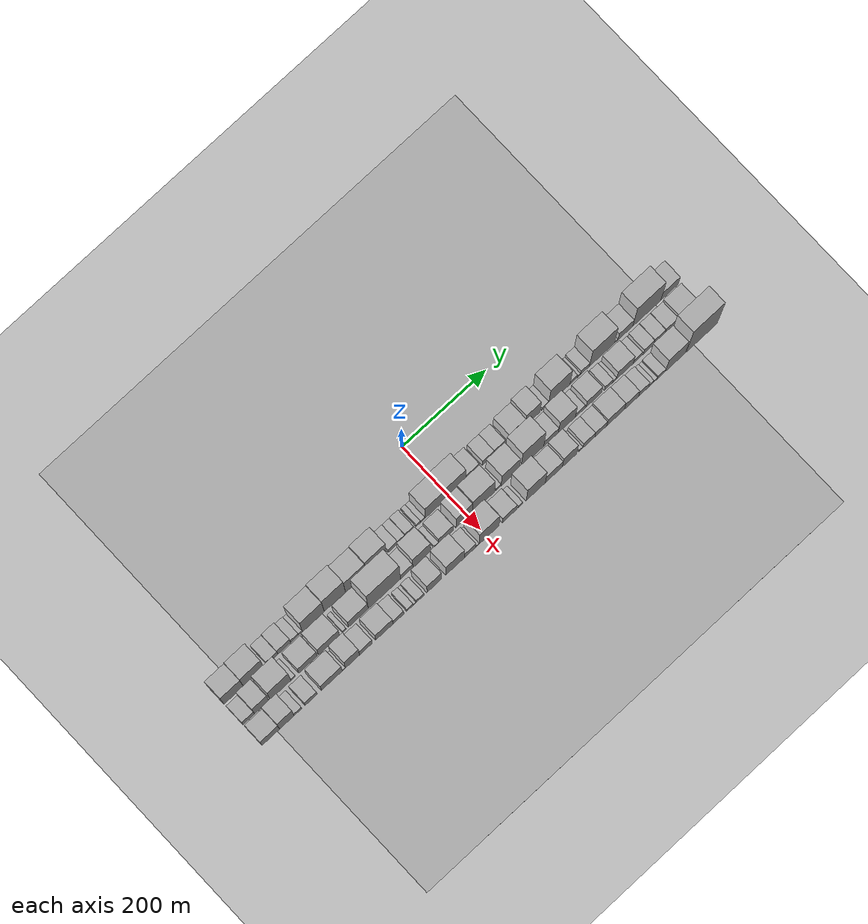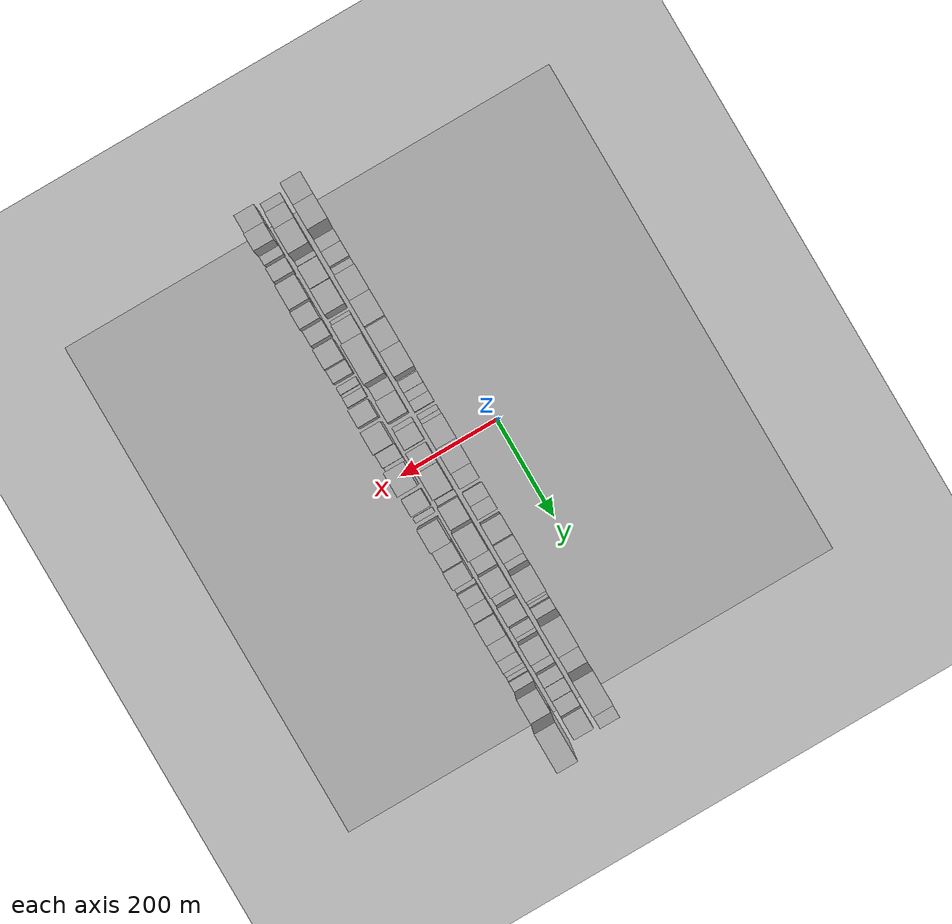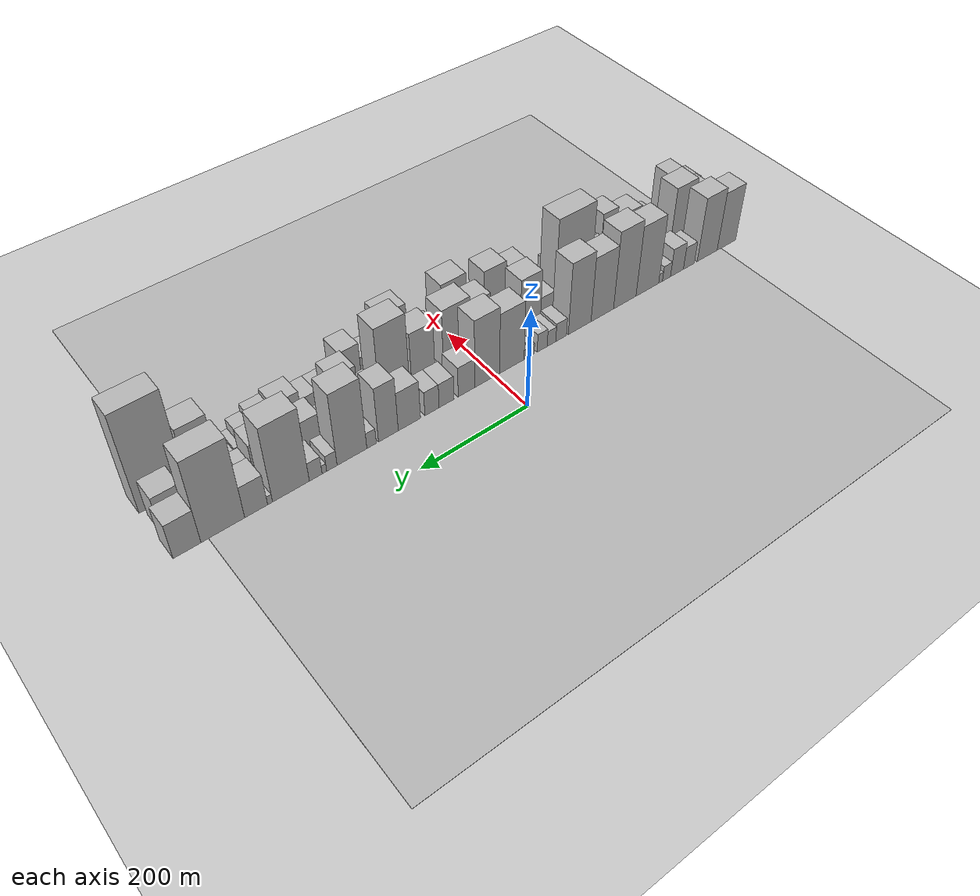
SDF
<?xml version="1.0" encoding="utf-8"?>

<sdf version="1.6">

   <world name="default">

      <gui fullscreen="0">

         <camera name="user_camera">

            <pose>-15 0 4.57585 0 0 0</pose>

            <view_controller>orbit</view_controller>

         </camera>

      </gui>

      <scene>

         <sky>

           <clouds>

             <speed>12</speed>

           </clouds>

         </sky>

         <ambient>0.4 0.4 0.4 1</ambient>

         <background>0.7 0.7 0.7 1</background>

         <shadows>1</shadows>

      </scene>

      <gravity>0 0 -9.8066</gravity>

      <magnetic_field>6e-06 2.3e-05 -4.2e-05</magnetic_field>

      <physics default="0" name="default_physics" type="ode">

         <ode>

            <solver>

               <type>quick</type>

               <iters>10</iters>

               <sor>1.0</sor>

               <use_dynamic_moi_rescaling>0</use_dynamic_moi_rescaling>

            </solver>

            <constraints>

               <cfm>0</cfm>

               <erp>0.2</erp>

               <contact_max_correcting_vel>100</contact_max_correcting_vel>

               <contact_surface_layer>0.001</contact_surface_layer>

            </constraints>

         </ode>

         <max_step_size>0.004</max_step_size>

         <real_time_factor>1</real_time_factor>

         <real_time_update_rate>250</real_time_update_rate>

      </physics>

      <light name="sun" type="directional">

         <cast_shadows>1</cast_shadows>

         <pose>0 0 10 0 0 0</pose>

         <diffuse>0.8 0.8 0.8 1</diffuse>

         <specular>0.2 0.2 0.2 1</specular>

         <attenuation>

            <range>1000</range>

            <constant>0.9</constant>

            <linear>0.01</linear>

            <quadratic>0.001</quadratic>

         </attenuation>

         <direction>-0.5 0.1 -0.9</direction>

      </light>

      <include>

         <name>ground_plane_1</name>

         <uri>model://HANNAS_ground_plane</uri>

         <pose>0 0 0  0 0 0</pose>

      </include>

      <include>

         <name>ground_plane_2</name>

         <uri>model://HANNAS_ground_plane</uri>

         <pose>100 0 0  0 0 0</pose>

      </include>

      <model name="building_1">

         <static>1</static>

         <pose frame="">100.0000 -513.0311 0 0.000000 0.000000 0.000000</pose>

         <link name="link">

            <pose frame="">0 0 61.50 0 0 0</pose>

            <collision name="collision">

               <geometry>

                  <box>

                     <size>40.0000 45.9378 123.0000</size>

                  </box>

               </geometry>

               <max_contacts>10</max_contacts>

               <surface>

                  <contact>

                     <ode/>

                  </contact>

                  <bounce/>

                  <friction>

                     <torsional>

                        <ode/>

                     </torsional>

                     <ode/>

                  </friction>

               </surface>

            </collision>

            <visual name="visual">

               <cast_shadows>0</cast_shadows>

               <geometry>

                  <box>

                     <size>40.0000 45.9378 123.0000</size>

                  </box>

               </geometry>

               <material>

                  <script>

                     <uri>model://HANNAS_wall/materials/scripts</uri>

                     <uri>model://HANNAS_wall/materials/textures</uri>

                     <name>vrc/HANNAS_wall</name>

                  </script>

               </material>

            </visual>

            <self_collide>0</self_collide>

            <enable_wind>0</enable_wind>

            <kinematic>0</kinematic>

         </link>

      </model>

      <model name="building_2">

         <static>1</static>

         <pose frame="">100.0000 -465.8310 0 0.000000 0.000000 0.000000</pose>

         <link name="link">

            <pose frame="">0 0 67.50 0 0 0</pose>

            <collision name="collision">

               <geometry>

                  <box>

                     <size>40.0000 48.4624 135.0000</size>

                  </box>

               </geometry>

               <max_contacts>10</max_contacts>

               <surface>

                  <contact>

                     <ode/>

                  </contact>

                  <bounce/>

                  <friction>

                     <torsional>

                        <ode/>

                     </torsional>

                     <ode/>

                  </friction>

               </surface>

            </collision>

            <visual name="visual">

               <cast_shadows>0</cast_shadows>

               <geometry>

                  <box>

                     <size>40.0000 48.4624 135.0000</size>

                  </box>

               </geometry>

               <material>

                  <script>

                     <uri>model://HANNAS_wall/materials/scripts</uri>

                     <uri>model://HANNAS_wall/materials/textures</uri>

                     <name>vrc/HANNAS_wall</name>

                  </script>

               </material>

            </visual>

            <self_collide>0</self_collide>

            <enable_wind>0</enable_wind>

            <kinematic>0</kinematic>

         </link>

      </model>

      <model name="building_3">

         <static>1</static>

         <pose frame="">100.0000 -421.4794 0 0.000000 0.000000 0.000000</pose>

         <link name="link">

            <pose frame="">0 0 24.00 0 0 0</pose>

            <collision name="collision">

               <geometry>

                  <box>

                     <size>40.0000 26.2407 48.0000</size>

                  </box>

               </geometry>

               <max_contacts>10</max_contacts>

               <surface>

                  <contact>

                     <ode/>

                  </contact>

                  <bounce/>

                  <friction>

                     <torsional>

                        <ode/>

                     </torsional>

                     <ode/>

                  </friction>

               </surface>

            </collision>

            <visual name="visual">

               <cast_shadows>0</cast_shadows>

               <geometry>

                  <box>

                     <size>40.0000 26.2407 48.0000</size>

                  </box>

               </geometry>

               <material>

                  <script>

                     <uri>model://HANNAS_wall/materials/scripts</uri>

                     <uri>model://HANNAS_wall/materials/textures</uri>

                     <name>vrc/HANNAS_wall</name>

                  </script>

               </material>

            </visual>

            <self_collide>0</self_collide>

            <enable_wind>0</enable_wind>

            <kinematic>0</kinematic>

         </link>

      </model>

      <model name="building_4">

         <static>1</static>

         <pose frame="">100.0000 -393.1098 0 0.000000 0.000000 0.000000</pose>

         <link name="link">

            <pose frame="">0 0 30.00 0 0 0</pose>

            <collision name="collision">

               <geometry>

                  <box>

                     <size>40.0000 30.4985 60.0000</size>

                  </box>

               </geometry>

               <max_contacts>10</max_contacts>

               <surface>

                  <contact>

                     <ode/>

                  </contact>

                  <bounce/>

                  <friction>

                     <torsional>

                        <ode/>

                     </torsional>

                     <ode/>

                  </friction>

               </surface>

            </collision>

            <visual name="visual">

               <cast_shadows>0</cast_shadows>

               <geometry>

                  <box>

                     <size>40.0000 30.4985 60.0000</size>

                  </box>

               </geometry>

               <material>

                  <script>

                     <uri>model://HANNAS_wall/materials/scripts</uri>

                     <uri>model://HANNAS_wall/materials/textures</uri>

                     <name>vrc/HANNAS_wall</name>

                  </script>

               </material>

            </visual>

            <self_collide>0</self_collide>

            <enable_wind>0</enable_wind>

            <kinematic>0</kinematic>

         </link>

      </model>

      <model name="building_5">

         <static>1</static>

         <pose frame="">100.0000 -368.4196 0 0.000000 0.000000 0.000000</pose>

         <link name="link">

            <pose frame="">0 0 16.50 0 0 0</pose>

            <collision name="collision">

               <geometry>

                  <box>

                     <size>40.0000 18.8819 33.0000</size>

                  </box>

               </geometry>

               <max_contacts>10</max_contacts>

               <surface>

                  <contact>

                     <ode/>

                  </contact>

                  <bounce/>

                  <friction>

                     <torsional>

                        <ode/>

                     </torsional>

                     <ode/>

                  </friction>

               </surface>

            </collision>

            <visual name="visual">

               <cast_shadows>0</cast_shadows>

               <geometry>

                  <box>

                     <size>40.0000 18.8819 33.0000</size>

                  </box>

               </geometry>

               <material>

                  <script>

                     <uri>model://HANNAS_wall/materials/scripts</uri>

                     <uri>model://HANNAS_wall/materials/textures</uri>

                     <name>vrc/HANNAS_wall</name>

                  </script>

               </material>

            </visual>

            <self_collide>0</self_collide>

            <enable_wind>0</enable_wind>

            <kinematic>0</kinematic>

         </link>

      </model>

      <model name="building_6">

         <static>1</static>

         <pose frame="">100.0000 -354.5994 0 0.000000 0.000000 0.000000</pose>

         <link name="link">

            <pose frame="">0 0 10.50 0 0 0</pose>

            <collision name="collision">

               <geometry>

                  <box>

                     <size>40.0000 8.7584 21.0000</size>

                  </box>

               </geometry>

               <max_contacts>10</max_contacts>

               <surface>

                  <contact>

                     <ode/>

                  </contact>

                  <bounce/>

                  <friction>

                     <torsional>

                        <ode/>

                     </torsional>

                     <ode/>

                  </friction>

               </surface>

            </collision>

            <visual name="visual">

               <cast_shadows>0</cast_shadows>

               <geometry>

                  <box>

                     <size>40.0000 8.7584 21.0000</size>

                  </box>

               </geometry>

               <material>

                  <script>

                     <uri>model://HANNAS_wall/materials/scripts</uri>

                     <uri>model://HANNAS_wall/materials/textures</uri>

                     <name>vrc/HANNAS_wall</name>

                  </script>

               </material>

            </visual>

            <self_collide>0</self_collide>

            <enable_wind>0</enable_wind>

            <kinematic>0</kinematic>

         </link>

      </model>

      <model name="building_7">

         <static>1</static>

         <pose frame="">100.0000 -324.2899 0 0.000000 0.000000 0.000000</pose>

         <link name="link">

            <pose frame="">0 0 73.50 0 0 0</pose>

            <collision name="collision">

               <geometry>

                  <box>

                     <size>40.0000 51.8606 147.0000</size>

                  </box>

               </geometry>

               <max_contacts>10</max_contacts>

               <surface>

                  <contact>

                     <ode/>

                  </contact>

                  <bounce/>

                  <friction>

                     <torsional>

                        <ode/>

                     </torsional>

                     <ode/>

                  </friction>

               </surface>

            </collision>

            <visual name="visual">

               <cast_shadows>0</cast_shadows>

               <geometry>

                  <box>

                     <size>40.0000 51.8606 147.0000</size>

                  </box>

               </geometry>

               <material>

                  <script>

                     <uri>model://HANNAS_wall/materials/scripts</uri>

                     <uri>model://HANNAS_wall/materials/textures</uri>

                     <name>vrc/HANNAS_wall</name>

                  </script>

               </material>

            </visual>

            <self_collide>0</self_collide>

            <enable_wind>0</enable_wind>

            <kinematic>0</kinematic>

         </link>

      </model>

      <model name="building_8">

         <static>1</static>

         <pose frame="">100.0000 -273.1659 0 0.000000 0.000000 0.000000</pose>

         <link name="link">

            <pose frame="">0 0 81.00 0 0 0</pose>

            <collision name="collision">

               <geometry>

                  <box>

                     <size>40.0000 50.3876 162.0000</size>

                  </box>

               </geometry>

               <max_contacts>10</max_contacts>

               <surface>

                  <contact>

                     <ode/>

                  </contact>

                  <bounce/>

                  <friction>

                     <torsional>

                        <ode/>

                     </torsional>

                     <ode/>

                  </friction>

               </surface>

            </collision>

            <visual name="visual">

               <cast_shadows>0</cast_shadows>

               <geometry>

                  <box>

                     <size>40.0000 50.3876 162.0000</size>

                  </box>

               </geometry>

               <material>

                  <script>

                     <uri>model://HANNAS_wall/materials/scripts</uri>

                     <uri>model://HANNAS_wall/materials/textures</uri>

                     <name>vrc/HANNAS_wall</name>

                  </script>

               </material>

            </visual>

            <self_collide>0</self_collide>

            <enable_wind>0</enable_wind>

            <kinematic>0</kinematic>

         </link>

      </model>

      <model name="building_9">

         <static>1</static>

         <pose frame="">100.0000 -223.2876 0 0.000000 0.000000 0.000000</pose>

         <link name="link">

            <pose frame="">0 0 67.50 0 0 0</pose>

            <collision name="collision">

               <geometry>

                  <box>

                     <size>40.0000 49.3688 135.0000</size>

                  </box>

               </geometry>

               <max_contacts>10</max_contacts>

               <surface>

                  <contact>

                     <ode/>

                  </contact>

                  <bounce/>

                  <friction>

                     <torsional>

                        <ode/>

                     </torsional>

                     <ode/>

                  </friction>

               </surface>

            </collision>

            <visual name="visual">

               <cast_shadows>0</cast_shadows>

               <geometry>

                  <box>

                     <size>40.0000 49.3688 135.0000</size>

                  </box>

               </geometry>

               <material>

                  <script>

                     <uri>model://HANNAS_wall/materials/scripts</uri>

                     <uri>model://HANNAS_wall/materials/textures</uri>

                     <name>vrc/HANNAS_wall</name>

                  </script>

               </material>

            </visual>

            <self_collide>0</self_collide>

            <enable_wind>0</enable_wind>

            <kinematic>0</kinematic>

         </link>

      </model>

      <model name="building_10">

         <static>1</static>

         <pose frame="">100.0000 -174.2582 0 0.000000 0.000000 0.000000</pose>

         <link name="link">

            <pose frame="">0 0 75.00 0 0 0</pose>

            <collision name="collision">

               <geometry>

                  <box>

                     <size>40.0000 48.6901 150.0000</size>

                  </box>

               </geometry>

               <max_contacts>10</max_contacts>

               <surface>

                  <contact>

                     <ode/>

                  </contact>

                  <bounce/>

                  <friction>

                     <torsional>

                        <ode/>

                     </torsional>

                     <ode/>

                  </friction>

               </surface>

            </collision>

            <visual name="visual">

               <cast_shadows>0</cast_shadows>

               <geometry>

                  <box>

                     <size>40.0000 48.6901 150.0000</size>

                  </box>

               </geometry>

               <material>

                  <script>

                     <uri>model://HANNAS_wall/materials/scripts</uri>

                     <uri>model://HANNAS_wall/materials/textures</uri>

                     <name>vrc/HANNAS_wall</name>

                  </script>

               </material>

            </visual>

            <self_collide>0</self_collide>

            <enable_wind>0</enable_wind>

            <kinematic>0</kinematic>

         </link>

      </model>

      <model name="building_11">

         <static>1</static>

         <pose frame="">100.0000 -134.7370 0 0.000000 0.000000 0.000000</pose>

         <link name="link">

            <pose frame="">0 0 19.50 0 0 0</pose>

            <collision name="collision">

               <geometry>

                  <box>

                     <size>40.0000 22.3522 39.0000</size>

                  </box>

               </geometry>

               <max_contacts>10</max_contacts>

               <surface>

                  <contact>

                     <ode/>

                  </contact>

                  <bounce/>

                  <friction>

                     <torsional>

                        <ode/>

                     </torsional>

                     <ode/>

                  </friction>

               </surface>

            </collision>

            <visual name="visual">

               <cast_shadows>0</cast_shadows>

               <geometry>

                  <box>

                     <size>40.0000 22.3522 39.0000</size>

                  </box>

               </geometry>

               <material>

                  <script>

                     <uri>model://HANNAS_wall/materials/scripts</uri>

                     <uri>model://HANNAS_wall/materials/textures</uri>

                     <name>vrc/HANNAS_wall</name>

                  </script>

               </material>

            </visual>

            <self_collide>0</self_collide>

            <enable_wind>0</enable_wind>

            <kinematic>0</kinematic>

         </link>

      </model>

      <model name="building_12">

         <static>1</static>

         <pose frame="">100.0000 -114.6446 0 0.000000 0.000000 0.000000</pose>

         <link name="link">

            <pose frame="">0 0 16.50 0 0 0</pose>

            <collision name="collision">

               <geometry>

                  <box>

                     <size>40.0000 17.8327 33.0000</size>

                  </box>

               </geometry>

               <max_contacts>10</max_contacts>

               <surface>

                  <contact>

                     <ode/>

                  </contact>

                  <bounce/>

                  <friction>

                     <torsional>

                        <ode/>

                     </torsional>

                     <ode/>

                  </friction>

               </surface>

            </collision>

            <visual name="visual">

               <cast_shadows>0</cast_shadows>

               <geometry>

                  <box>

                     <size>40.0000 17.8327 33.0000</size>

                  </box>

               </geometry>

               <material>

                  <script>

                     <uri>model://HANNAS_wall/materials/scripts</uri>

                     <uri>model://HANNAS_wall/materials/textures</uri>

                     <name>vrc/HANNAS_wall</name>

                  </script>

               </material>

            </visual>

            <self_collide>0</self_collide>

            <enable_wind>0</enable_wind>

            <kinematic>0</kinematic>

         </link>

      </model>

      <model name="building_13">

         <static>1</static>

         <pose frame="">100.0000 -95.3053 0 0.000000 0.000000 0.000000</pose>

         <link name="link">

            <pose frame="">0 0 19.50 0 0 0</pose>

            <collision name="collision">

               <geometry>

                  <box>

                     <size>40.0000 20.8459 39.0000</size>

                  </box>

               </geometry>

               <max_contacts>10</max_contacts>

               <surface>

                  <contact>

                     <ode/>

                  </contact>

                  <bounce/>

                  <friction>

                     <torsional>

                        <ode/>

                     </torsional>

                     <ode/>

                  </friction>

               </surface>

            </collision>

            <visual name="visual">

               <cast_shadows>0</cast_shadows>

               <geometry>

                  <box>

                     <size>40.0000 20.8459 39.0000</size>

                  </box>

               </geometry>

               <material>

                  <script>

                     <uri>model://HANNAS_wall/materials/scripts</uri>

                     <uri>model://HANNAS_wall/materials/textures</uri>

                     <name>vrc/HANNAS_wall</name>

                  </script>

               </material>

            </visual>

            <self_collide>0</self_collide>

            <enable_wind>0</enable_wind>

            <kinematic>0</kinematic>

         </link>

      </model>

      <model name="building_14">

         <static>1</static>

         <pose frame="">100.0000 -73.6929 0 0.000000 0.000000 0.000000</pose>

         <link name="link">

            <pose frame="">0 0 12.00 0 0 0</pose>

            <collision name="collision">

               <geometry>

                  <box>

                     <size>40.0000 10.3789 24.0000</size>

                  </box>

               </geometry>

               <max_contacts>10</max_contacts>

               <surface>

                  <contact>

                     <ode/>

                  </contact>

                  <bounce/>

                  <friction>

                     <torsional>

                        <ode/>

                     </torsional>

                     <ode/>

                  </friction>

               </surface>

            </collision>

            <visual name="visual">

               <cast_shadows>0</cast_shadows>

               <geometry>

                  <box>

                     <size>40.0000 10.3789 24.0000</size>

                  </box>

               </geometry>

               <material>

                  <script>

                     <uri>model://HANNAS_wall/materials/scripts</uri>

                     <uri>model://HANNAS_wall/materials/textures</uri>

                     <name>vrc/HANNAS_wall</name>

                  </script>

               </material>

            </visual>

            <self_collide>0</self_collide>

            <enable_wind>0</enable_wind>

            <kinematic>0</kinematic>

         </link>

      </model>

      <model name="building_15">

         <static>1</static>

         <pose frame="">100.0000 -63.2719 0 0.000000 0.000000 0.000000</pose>

         <link name="link">

            <pose frame="">0 0 10.50 0 0 0</pose>

            <collision name="collision">

               <geometry>

                  <box>

                     <size>40.0000 10.4631 21.0000</size>

                  </box>

               </geometry>

               <max_contacts>10</max_contacts>

               <surface>

                  <contact>

                     <ode/>

                  </contact>

                  <bounce/>

                  <friction>

                     <torsional>

                        <ode/>

                     </torsional>

                     <ode/>

                  </friction>

               </surface>

            </collision>

            <visual name="visual">

               <cast_shadows>0</cast_shadows>

               <geometry>

                  <box>

                     <size>40.0000 10.4631 21.0000</size>

                  </box>

               </geometry>

               <material>

                  <script>

                     <uri>model://HANNAS_wall/materials/scripts</uri>

                     <uri>model://HANNAS_wall/materials/textures</uri>

                     <name>vrc/HANNAS_wall</name>

                  </script>

               </material>

            </visual>

            <self_collide>0</self_collide>

            <enable_wind>0</enable_wind>

            <kinematic>0</kinematic>

         </link>

      </model>

      <model name="building_16">

         <static>1</static>

         <pose frame="">100.0000 -33.5212 0 0.000000 0.000000 0.000000</pose>

         <link name="link">

            <pose frame="">0 0 63.00 0 0 0</pose>

            <collision name="collision">

               <geometry>

                  <box>

                     <size>40.0000 49.0381 126.0000</size>

                  </box>

               </geometry>

               <max_contacts>10</max_contacts>

               <surface>

                  <contact>

                     <ode/>

                  </contact>

                  <bounce/>

                  <friction>

                     <torsional>

                        <ode/>

                     </torsional>

                     <ode/>

                  </friction>

               </surface>

            </collision>

            <visual name="visual">

               <cast_shadows>0</cast_shadows>

               <geometry>

                  <box>

                     <size>40.0000 49.0381 126.0000</size>

                  </box>

               </geometry>

               <material>

                  <script>

                     <uri>model://HANNAS_wall/materials/scripts</uri>

                     <uri>model://HANNAS_wall/materials/textures</uri>

                     <name>vrc/HANNAS_wall</name>

                  </script>

               </material>

            </visual>

            <self_collide>0</self_collide>

            <enable_wind>0</enable_wind>

            <kinematic>0</kinematic>

         </link>

      </model>

      <model name="building_17">

         <static>1</static>

         <pose frame="">100.0000 15.3192 0 0.000000 0.000000 0.000000</pose>

         <link name="link">

            <pose frame="">0 0 70.50 0 0 0</pose>

            <collision name="collision">

               <geometry>

                  <box>

                     <size>40.0000 48.6428 141.0000</size>

                  </box>

               </geometry>

               <max_contacts>10</max_contacts>

               <surface>

                  <contact>

                     <ode/>

                  </contact>

                  <bounce/>

                  <friction>

                     <torsional>

                        <ode/>

                     </torsional>

                     <ode/>

                  </friction>

               </surface>

            </collision>

            <visual name="visual">

               <cast_shadows>0</cast_shadows>

               <geometry>

                  <box>

                     <size>40.0000 48.6428 141.0000</size>

                  </box>

               </geometry>

               <material>

                  <script>

                     <uri>model://HANNAS_wall/materials/scripts</uri>

                     <uri>model://HANNAS_wall/materials/textures</uri>

                     <name>vrc/HANNAS_wall</name>

                  </script>

               </material>

            </visual>

            <self_collide>0</self_collide>

            <enable_wind>0</enable_wind>

            <kinematic>0</kinematic>

         </link>

      </model>

      <model name="building_18">

         <static>1</static>

         <pose frame="">100.0000 55.6882 0 0.000000 0.000000 0.000000</pose>

         <link name="link">

            <pose frame="">0 0 31.50 0 0 0</pose>

            <collision name="collision">

               <geometry>

                  <box>

                     <size>40.0000 32.0952 63.0000</size>

                  </box>

               </geometry>

               <max_contacts>10</max_contacts>

               <surface>

                  <contact>

                     <ode/>

                  </contact>

                  <bounce/>

                  <friction>

                     <torsional>

                        <ode/>

                     </torsional>

                     <ode/>

                  </friction>

               </surface>

            </collision>

            <visual name="visual">

               <cast_shadows>0</cast_shadows>

               <geometry>

                  <box>

                     <size>40.0000 32.0952 63.0000</size>

                  </box>

               </geometry>

               <material>

                  <script>

                     <uri>model://HANNAS_wall/materials/scripts</uri>

                     <uri>model://HANNAS_wall/materials/textures</uri>

                     <name>vrc/HANNAS_wall</name>

                  </script>

               </material>

            </visual>

            <self_collide>0</self_collide>

            <enable_wind>0</enable_wind>

            <kinematic>0</kinematic>

         </link>

      </model>

      <model name="building_19">

         <static>1</static>

         <pose frame="">100.0000 93.7765 0 0.000000 0.000000 0.000000</pose>

         <link name="link">

            <pose frame="">0 0 25.50 0 0 0</pose>

            <collision name="collision">

               <geometry>

                  <box>

                     <size>40.0000 28.0813 51.0000</size>

                  </box>

               </geometry>

               <max_contacts>10</max_contacts>

               <surface>

                  <contact>

                     <ode/>

                  </contact>

                  <bounce/>

                  <friction>

                     <torsional>

                        <ode/>

                     </torsional>

                     <ode/>

                  </friction>

               </surface>

            </collision>

            <visual name="visual">

               <cast_shadows>0</cast_shadows>

               <geometry>

                  <box>

                     <size>40.0000 28.0813 51.0000</size>

                  </box>

               </geometry>

               <material>

                  <script>

                     <uri>model://HANNAS_wall/materials/scripts</uri>

                     <uri>model://HANNAS_wall/materials/textures</uri>

                     <name>vrc/HANNAS_wall</name>

                  </script>

               </material>

            </visual>

            <self_collide>0</self_collide>

            <enable_wind>0</enable_wind>

            <kinematic>0</kinematic>

         </link>

      </model>

      <model name="building_20">

         <static>1</static>

         <pose frame="">100.0000 121.1682 0 0.000000 0.000000 0.000000</pose>

         <link name="link">

            <pose frame="">0 0 25.50 0 0 0</pose>

            <collision name="collision">

               <geometry>

                  <box>

                     <size>40.0000 26.7020 51.0000</size>

                  </box>

               </geometry>

               <max_contacts>10</max_contacts>

               <surface>

                  <contact>

                     <ode/>

                  </contact>

                  <bounce/>

                  <friction>

                     <torsional>

                        <ode/>

                     </torsional>

                     <ode/>

                  </friction>

               </surface>

            </collision>

            <visual name="visual">

               <cast_shadows>0</cast_shadows>

               <geometry>

                  <box>

                     <size>40.0000 26.7020 51.0000</size>

                  </box>

               </geometry>

               <material>

                  <script>

                     <uri>model://HANNAS_wall/materials/scripts</uri>

                     <uri>model://HANNAS_wall/materials/textures</uri>

                     <name>vrc/HANNAS_wall</name>

                  </script>

               </material>

            </visual>

            <self_collide>0</self_collide>

            <enable_wind>0</enable_wind>

            <kinematic>0</kinematic>

         </link>

      </model>

      <model name="building_21">

         <static>1</static>

         <pose frame="">100.0000 162.8495 0 0.000000 0.000000 0.000000</pose>

         <link name="link">

            <pose frame="">0 0 40.50 0 0 0</pose>

            <collision name="collision">

               <geometry>

                  <box>

                     <size>40.0000 40.6607 81.0000</size>

                  </box>

               </geometry>

               <max_contacts>10</max_contacts>

               <surface>

                  <contact>

                     <ode/>

                  </contact>

                  <bounce/>

                  <friction>

                     <torsional>

                        <ode/>

                     </torsional>

                     <ode/>

                  </friction>

               </surface>

            </collision>

            <visual name="visual">

               <cast_shadows>0</cast_shadows>

               <geometry>

                  <box>

                     <size>40.0000 40.6607 81.0000</size>

                  </box>

               </geometry>

               <material>

                  <script>

                     <uri>model://HANNAS_wall/materials/scripts</uri>

                     <uri>model://HANNAS_wall/materials/textures</uri>

                     <name>vrc/HANNAS_wall</name>

                  </script>

               </material>

            </visual>

            <self_collide>0</self_collide>

            <enable_wind>0</enable_wind>

            <kinematic>0</kinematic>

         </link>

      </model>

      <model name="building_22">

         <static>1</static>

         <pose frame="">100.0000 200.8894 0 0.000000 0.000000 0.000000</pose>

         <link name="link">

            <pose frame="">0 0 57.00 0 0 0</pose>

            <collision name="collision">

               <geometry>

                  <box>

                     <size>40.0000 35.4190 114.0000</size>

                  </box>

               </geometry>

               <max_contacts>10</max_contacts>

               <surface>

                  <contact>

                     <ode/>

                  </contact>

                  <bounce/>

                  <friction>

                     <torsional>

                        <ode/>

                     </torsional>

                     <ode/>

                  </friction>

               </surface>

            </collision>

            <visual name="visual">

               <cast_shadows>0</cast_shadows>

               <geometry>

                  <box>

                     <size>40.0000 35.4190 114.0000</size>

                  </box>

               </geometry>

               <material>

                  <script>

                     <uri>model://HANNAS_wall/materials/scripts</uri>

                     <uri>model://HANNAS_wall/materials/textures</uri>

                     <name>vrc/HANNAS_wall</name>

                  </script>

               </material>

            </visual>

            <self_collide>0</self_collide>

            <enable_wind>0</enable_wind>

            <kinematic>0</kinematic>

         </link>

      </model>

      <model name="building_23">

         <static>1</static>

         <pose frame="">100.0000 230.9444 0 0.000000 0.000000 0.000000</pose>

         <link name="link">

            <pose frame="">0 0 16.50 0 0 0</pose>

            <collision name="collision">

               <geometry>

                  <box>

                     <size>40.0000 16.6910 33.0000</size>

                  </box>

               </geometry>

               <max_contacts>10</max_contacts>

               <surface>

                  <contact>

                     <ode/>

                  </contact>

                  <bounce/>

                  <friction>

                     <torsional>

                        <ode/>

                     </torsional>

                     <ode/>

                  </friction>

               </surface>

            </collision>

            <visual name="visual">

               <cast_shadows>0</cast_shadows>

               <geometry>

                  <box>

                     <size>40.0000 16.6910 33.0000</size>

                  </box>

               </geometry>

               <material>

                  <script>

                     <uri>model://HANNAS_wall/materials/scripts</uri>

                     <uri>model://HANNAS_wall/materials/textures</uri>

                     <name>vrc/HANNAS_wall</name>

                  </script>

               </material>

            </visual>

            <self_collide>0</self_collide>

            <enable_wind>0</enable_wind>

            <kinematic>0</kinematic>

         </link>

      </model>

      <model name="building_24">

         <static>1</static>

         <pose frame="">100.0000 265.1523 0 0.000000 0.000000 0.000000</pose>

         <link name="link">

            <pose frame="">0 0 75.00 0 0 0</pose>

            <collision name="collision">

               <geometry>

                  <box>

                     <size>40.0000 51.7249 150.0000</size>

                  </box>

               </geometry>

               <max_contacts>10</max_contacts>

               <surface>

                  <contact>

                     <ode/>

                  </contact>

                  <bounce/>

                  <friction>

                     <torsional>

                        <ode/>

                     </torsional>

                     <ode/>

                  </friction>

               </surface>

            </collision>

            <visual name="visual">

               <cast_shadows>0</cast_shadows>

               <geometry>

                  <box>

                     <size>40.0000 51.7249 150.0000</size>

                  </box>

               </geometry>

               <material>

                  <script>

                     <uri>model://HANNAS_wall/materials/scripts</uri>

                     <uri>model://HANNAS_wall/materials/textures</uri>

                     <name>vrc/HANNAS_wall</name>

                  </script>

               </material>

            </visual>

            <self_collide>0</self_collide>

            <enable_wind>0</enable_wind>

            <kinematic>0</kinematic>

         </link>

      </model>

      <model name="building_25">

         <static>1</static>

         <pose frame="">100.0000 299.8778 0 0.000000 0.000000 0.000000</pose>

         <link name="link">

            <pose frame="">0 0 16.50 0 0 0</pose>

            <collision name="collision">

               <geometry>

                  <box>

                     <size>40.0000 17.7260 33.0000</size>

                  </box>

               </geometry>

               <max_contacts>10</max_contacts>

               <surface>

                  <contact>

                     <ode/>

                  </contact>

                  <bounce/>

                  <friction>

                     <torsional>

                        <ode/>

                     </torsional>

                     <ode/>

                  </friction>

               </surface>

            </collision>

            <visual name="visual">

               <cast_shadows>0</cast_shadows>

               <geometry>

                  <box>

                     <size>40.0000 17.7260 33.0000</size>

                  </box>

               </geometry>

               <material>

                  <script>

                     <uri>model://HANNAS_wall/materials/scripts</uri>

                     <uri>model://HANNAS_wall/materials/textures</uri>

                     <name>vrc/HANNAS_wall</name>

                  </script>

               </material>

            </visual>

            <self_collide>0</self_collide>

            <enable_wind>0</enable_wind>

            <kinematic>0</kinematic>

         </link>

      </model>

      <model name="building_26">

         <static>1</static>

         <pose frame="">100.0000 312.5977 0 0.000000 0.000000 0.000000</pose>

         <link name="link">

            <pose frame="">0 0 9.00 0 0 0</pose>

            <collision name="collision">

               <geometry>

                  <box>

                     <size>40.0000 7.7139 18.0000</size>

                  </box>

               </geometry>

               <max_contacts>10</max_contacts>

               <surface>

                  <contact>

                     <ode/>

                  </contact>

                  <bounce/>

                  <friction>

                     <torsional>

                        <ode/>

                     </torsional>

                     <ode/>

                  </friction>

               </surface>

            </collision>

            <visual name="visual">

               <cast_shadows>0</cast_shadows>

               <geometry>

                  <box>

                     <size>40.0000 7.7139 18.0000</size>

                  </box>

               </geometry>

               <material>

                  <script>

                     <uri>model://HANNAS_wall/materials/scripts</uri>

                     <uri>model://HANNAS_wall/materials/textures</uri>

                     <name>vrc/HANNAS_wall</name>

                  </script>

               </material>

            </visual>

            <self_collide>0</self_collide>

            <enable_wind>0</enable_wind>

            <kinematic>0</kinematic>

         </link>

      </model>

      <model name="building_27">

         <static>1</static>

         <pose frame="">100.0000 327.2426 0 0.000000 0.000000 0.000000</pose>

         <link name="link">

            <pose frame="">0 0 19.50 0 0 0</pose>

            <collision name="collision">

               <geometry>

                  <box>

                     <size>40.0000 21.5758 39.0000</size>

                  </box>

               </geometry>

               <max_contacts>10</max_contacts>

               <surface>

                  <contact>

                     <ode/>

                  </contact>

                  <bounce/>

                  <friction>

                     <torsional>

                        <ode/>

                     </torsional>

                     <ode/>

                  </friction>

               </surface>

            </collision>

            <visual name="visual">

               <cast_shadows>0</cast_shadows>

               <geometry>

                  <box>

                     <size>40.0000 21.5758 39.0000</size>

                  </box>

               </geometry>

               <material>

                  <script>

                     <uri>model://HANNAS_wall/materials/scripts</uri>

                     <uri>model://HANNAS_wall/materials/textures</uri>

                     <name>vrc/HANNAS_wall</name>

                  </script>

               </material>

            </visual>

            <self_collide>0</self_collide>

            <enable_wind>0</enable_wind>

            <kinematic>0</kinematic>

         </link>

      </model>

      <model name="building_28">

         <static>1</static>

         <pose frame="">100.0000 368.3218 0 0.000000 0.000000 0.000000</pose>

         <link name="link">

            <pose frame="">0 0 78.00 0 0 0</pose>

            <collision name="collision">

               <geometry>

                  <box>

                     <size>40.0000 60.5826 156.0000</size>

                  </box>

               </geometry>

               <max_contacts>10</max_contacts>

               <surface>

                  <contact>

                     <ode/>

                  </contact>

                  <bounce/>

                  <friction>

                     <torsional>

                        <ode/>

                     </torsional>

                     <ode/>

                  </friction>

               </surface>

            </collision>

            <visual name="visual">

               <cast_shadows>0</cast_shadows>

               <geometry>

                  <box>

                     <size>40.0000 60.5826 156.0000</size>

                  </box>

               </geometry>

               <material>

                  <script>

                     <uri>model://HANNAS_wall/materials/scripts</uri>

                     <uri>model://HANNAS_wall/materials/textures</uri>

                     <name>vrc/HANNAS_wall</name>

                  </script>

               </material>

            </visual>

            <self_collide>0</self_collide>

            <enable_wind>0</enable_wind>

            <kinematic>0</kinematic>

         </link>

      </model>

      <model name="building_29">

         <static>1</static>

         <pose frame="">100.0000 402.6213 0 0.000000 0.000000 0.000000</pose>

         <link name="link">

            <pose frame="">0 0 9.00 0 0 0</pose>

            <collision name="collision">

               <geometry>

                  <box>

                     <size>40.0000 8.0165 18.0000</size>

                  </box>

               </geometry>

               <max_contacts>10</max_contacts>

               <surface>

                  <contact>

                     <ode/>

                  </contact>

                  <bounce/>

                  <friction>

                     <torsional>

                        <ode/>

                     </torsional>

                     <ode/>

                  </friction>

               </surface>

            </collision>

            <visual name="visual">

               <cast_shadows>0</cast_shadows>

               <geometry>

                  <box>

                     <size>40.0000 8.0165 18.0000</size>

                  </box>

               </geometry>

               <material>

                  <script>

                     <uri>model://HANNAS_wall/materials/scripts</uri>

                     <uri>model://HANNAS_wall/materials/textures</uri>

                     <name>vrc/HANNAS_wall</name>

                  </script>

               </material>

            </visual>

            <self_collide>0</self_collide>

            <enable_wind>0</enable_wind>

            <kinematic>0</kinematic>

         </link>

      </model>

      <model name="building_30">

         <static>1</static>

         <pose frame="">100.0000 424.9119 0 0.000000 0.000000 0.000000</pose>

         <link name="link">

            <pose frame="">0 0 33.00 0 0 0</pose>

            <collision name="collision">

               <geometry>

                  <box>

                     <size>40.0000 36.5647 66.0000</size>

                  </box>

               </geometry>

               <max_contacts>10</max_contacts>

               <surface>

                  <contact>

                     <ode/>

                  </contact>

                  <bounce/>

                  <friction>

                     <torsional>

                        <ode/>

                     </torsional>

                     <ode/>

                  </friction>

               </surface>

            </collision>

            <visual name="visual">

               <cast_shadows>0</cast_shadows>

               <geometry>

                  <box>

                     <size>40.0000 36.5647 66.0000</size>

                  </box>

               </geometry>

               <material>

                  <script>

                     <uri>model://HANNAS_wall/materials/scripts</uri>

                     <uri>model://HANNAS_wall/materials/textures</uri>

                     <name>vrc/HANNAS_wall</name>

                  </script>

               </material>

            </visual>

            <self_collide>0</self_collide>

            <enable_wind>0</enable_wind>

            <kinematic>0</kinematic>

         </link>

      </model>

      <model name="building_31">

         <static>1</static>

         <pose frame="">100.0000 477.3125 0 0.000000 0.000000 0.000000</pose>

         <link name="link">

            <pose frame="">0 0 85.50 0 0 0</pose>

            <collision name="collision">

               <geometry>

                  <box>

                     <size>40.0000 68.2364 171.0000</size>

                  </box>

               </geometry>

               <max_contacts>10</max_contacts>

               <surface>

                  <contact>

                     <ode/>

                  </contact>

                  <bounce/>

                  <friction>

                     <torsional>

                        <ode/>

                     </torsional>

                     <ode/>

                  </friction>

               </surface>

            </collision>

            <visual name="visual">

               <cast_shadows>0</cast_shadows>

               <geometry>

                  <box>

                     <size>40.0000 68.2364 171.0000</size>

                  </box>

               </geometry>

               <material>

                  <script>

                     <uri>model://HANNAS_wall/materials/scripts</uri>

                     <uri>model://HANNAS_wall/materials/textures</uri>

                     <name>vrc/HANNAS_wall</name>

                  </script>

               </material>

            </visual>

            <self_collide>0</self_collide>

            <enable_wind>0</enable_wind>

            <kinematic>0</kinematic>

         </link>

      </model>

      <model name="building_32">

         <static>1</static>

         <pose frame="">100.0000 532.5778 0 0.000000 0.000000 0.000000</pose>

         <link name="link">

            <pose frame="">0 0 36.00 0 0 0</pose>

            <collision name="collision">

               <geometry>

                  <box>

                     <size>40.0000 42.2942 72.0000</size>

                  </box>

               </geometry>

               <max_contacts>10</max_contacts>

               <surface>

                  <contact>

                     <ode/>

                  </contact>

                  <bounce/>

                  <friction>

                     <torsional>

                        <ode/>

                     </torsional>

                     <ode/>

                  </friction>

               </surface>

            </collision>

            <visual name="visual">

               <cast_shadows>0</cast_shadows>

               <geometry>

                  <box>

                     <size>40.0000 42.2942 72.0000</size>

                  </box>

               </geometry>

               <material>

                  <script>

                     <uri>model://HANNAS_wall/materials/scripts</uri>

                     <uri>model://HANNAS_wall/materials/textures</uri>

                     <name>vrc/HANNAS_wall</name>

                  </script>

               </material>

            </visual>

            <self_collide>0</self_collide>

            <enable_wind>0</enable_wind>

            <kinematic>0</kinematic>

         </link>

      </model>

      <model name="building_33">

         <static>1</static>

         <pose frame="">149.0000 -522.2949 0 0.000000 0.000000 0.000000</pose>

         <link name="link">

            <pose frame="">0 0 25.50 0 0 0</pose>

            <collision name="collision">

               <geometry>

                  <box>

                     <size>40.0000 27.4102 51.0000</size>

                  </box>

               </geometry>

               <max_contacts>10</max_contacts>

               <surface>

                  <contact>

                     <ode/>

                  </contact>

                  <bounce/>

                  <friction>

                     <torsional>

                        <ode/>

                     </torsional>

                     <ode/>

                  </friction>

               </surface>

            </collision>

            <visual name="visual">

               <cast_shadows>0</cast_shadows>

               <geometry>

                  <box>

                     <size>40.0000 27.4102 51.0000</size>

                  </box>

               </geometry>

               <material>

                  <script>

                     <uri>model://HANNAS_wall/materials/scripts</uri>

                     <uri>model://HANNAS_wall/materials/textures</uri>

                     <name>vrc/HANNAS_wall</name>

                  </script>

               </material>

            </visual>

            <self_collide>0</self_collide>

            <enable_wind>0</enable_wind>

            <kinematic>0</kinematic>

         </link>

      </model>

      <model name="building_34">

         <static>1</static>

         <pose frame="">149.0000 -491.5027 0 0.000000 0.000000 0.000000</pose>

         <link name="link">

            <pose frame="">0 0 52.50 0 0 0</pose>

            <collision name="collision">

               <geometry>

                  <box>

                     <size>40.0000 34.1741 105.0000</size>

                  </box>

               </geometry>

               <max_contacts>10</max_contacts>

               <surface>

                  <contact>

                     <ode/>

                  </contact>

                  <bounce/>

                  <friction>

                     <torsional>

                        <ode/>

                     </torsional>

                     <ode/>

                  </friction>

               </surface>

            </collision>

            <visual name="visual">

               <cast_shadows>0</cast_shadows>

               <geometry>

                  <box>

                     <size>40.0000 34.1741 105.0000</size>

                  </box>

               </geometry>

               <material>

                  <script>

                     <uri>model://HANNAS_wall/materials/scripts</uri>

                     <uri>model://HANNAS_wall/materials/textures</uri>

                     <name>vrc/HANNAS_wall</name>

                  </script>

               </material>

            </visual>

            <self_collide>0</self_collide>

            <enable_wind>0</enable_wind>

            <kinematic>0</kinematic>

         </link>

      </model>

      <model name="building_35">

         <static>1</static>

         <pose frame="">149.0000 -446.9399 0 0.000000 0.000000 0.000000</pose>

         <link name="link">

            <pose frame="">0 0 67.50 0 0 0</pose>

            <collision name="collision">

               <geometry>

                  <box>

                     <size>40.0000 48.9515 135.0000</size>

                  </box>

               </geometry>

               <max_contacts>10</max_contacts>

               <surface>

                  <contact>

                     <ode/>

                  </contact>

                  <bounce/>

                  <friction>

                     <torsional>

                        <ode/>

                     </torsional>

                     <ode/>

                  </friction>

               </surface>

            </collision>

            <visual name="visual">

               <cast_shadows>0</cast_shadows>

               <geometry>

                  <box>

                     <size>40.0000 48.9515 135.0000</size>

                  </box>

               </geometry>

               <material>

                  <script>

                     <uri>model://HANNAS_wall/materials/scripts</uri>

                     <uri>model://HANNAS_wall/materials/textures</uri>

                     <name>vrc/HANNAS_wall</name>

                  </script>

               </material>

            </visual>

            <self_collide>0</self_collide>

            <enable_wind>0</enable_wind>

            <kinematic>0</kinematic>

         </link>

      </model>

      <model name="building_36">

         <static>1</static>

         <pose frame="">149.0000 -417.2309 0 0.000000 0.000000 0.000000</pose>

         <link name="link">

            <pose frame="">0 0 12.00 0 0 0</pose>

            <collision name="collision">

               <geometry>

                  <box>

                     <size>40.0000 10.4664 24.0000</size>

                  </box>

               </geometry>

               <max_contacts>10</max_contacts>

               <surface>

                  <contact>

                     <ode/>

                  </contact>

                  <bounce/>

                  <friction>

                     <torsional>

                        <ode/>

                     </torsional>

                     <ode/>

                  </friction>

               </surface>

            </collision>

            <visual name="visual">

               <cast_shadows>0</cast_shadows>

               <geometry>

                  <box>

                     <size>40.0000 10.4664 24.0000</size>

                  </box>

               </geometry>

               <material>

                  <script>

                     <uri>model://HANNAS_wall/materials/scripts</uri>

                     <uri>model://HANNAS_wall/materials/textures</uri>

                     <name>vrc/HANNAS_wall</name>

                  </script>

               </material>

            </visual>

            <self_collide>0</self_collide>

            <enable_wind>0</enable_wind>

            <kinematic>0</kinematic>

         </link>

      </model>

      <model name="building_37">

         <static>1</static>

         <pose frame="">149.0000 -382.1430 0 0.000000 0.000000 0.000000</pose>

         <link name="link">

            <pose frame="">0 0 37.50 0 0 0</pose>

            <collision name="collision">

               <geometry>

                  <box>

                     <size>40.0000 43.7095 75.0000</size>

                  </box>

               </geometry>

               <max_contacts>10</max_contacts>

               <surface>

                  <contact>

                     <ode/>

                  </contact>

                  <bounce/>

                  <friction>

                     <torsional>

                        <ode/>

                     </torsional>

                     <ode/>

                  </friction>

               </surface>

            </collision>

            <visual name="visual">

               <cast_shadows>0</cast_shadows>

               <geometry>

                  <box>

                     <size>40.0000 43.7095 75.0000</size>

                  </box>

               </geometry>

               <material>

                  <script>

                     <uri>model://HANNAS_wall/materials/scripts</uri>

                     <uri>model://HANNAS_wall/materials/textures</uri>

                     <name>vrc/HANNAS_wall</name>

                  </script>

               </material>

            </visual>

            <self_collide>0</self_collide>

            <enable_wind>0</enable_wind>

            <kinematic>0</kinematic>

         </link>

      </model>

      <model name="building_38">

         <static>1</static>

         <pose frame="">149.0000 -332.1110 0 0.000000 0.000000 0.000000</pose>

         <link name="link">

            <pose frame="">0 0 45.00 0 0 0</pose>

            <collision name="collision">

               <geometry>

                  <box>

                     <size>40.0000 50.3545 90.0000</size>

                  </box>

               </geometry>

               <max_contacts>10</max_contacts>

               <surface>

                  <contact>

                     <ode/>

                  </contact>

                  <bounce/>

                  <friction>

                     <torsional>

                        <ode/>

                     </torsional>

                     <ode/>

                  </friction>

               </surface>

            </collision>

            <visual name="visual">

               <cast_shadows>0</cast_shadows>

               <geometry>

                  <box>

                     <size>40.0000 50.3545 90.0000</size>

                  </box>

               </geometry>

               <material>

                  <script>

                     <uri>model://HANNAS_wall/materials/scripts</uri>

                     <uri>model://HANNAS_wall/materials/textures</uri>

                     <name>vrc/HANNAS_wall</name>

                  </script>

               </material>

            </visual>

            <self_collide>0</self_collide>

            <enable_wind>0</enable_wind>

            <kinematic>0</kinematic>

         </link>

      </model>

      <model name="building_39">

         <static>1</static>

         <pose frame="">149.0000 -295.4854 0 0.000000 0.000000 0.000000</pose>

         <link name="link">

            <pose frame="">0 0 9.00 0 0 0</pose>

            <collision name="collision">

               <geometry>

                  <box>

                     <size>40.0000 8.8966 18.0000</size>

                  </box>

               </geometry>

               <max_contacts>10</max_contacts>

               <surface>

                  <contact>

                     <ode/>

                  </contact>

                  <bounce/>

                  <friction>

                     <torsional>

                        <ode/>

                     </torsional>

                     <ode/>

                  </friction>

               </surface>

            </collision>

            <visual name="visual">

               <cast_shadows>0</cast_shadows>

               <geometry>

                  <box>

                     <size>40.0000 8.8966 18.0000</size>

                  </box>

               </geometry>

               <material>

                  <script>

                     <uri>model://HANNAS_wall/materials/scripts</uri>

                     <uri>model://HANNAS_wall/materials/textures</uri>

                     <name>vrc/HANNAS_wall</name>

                  </script>

               </material>

            </visual>

            <self_collide>0</self_collide>

            <enable_wind>0</enable_wind>

            <kinematic>0</kinematic>

         </link>

      </model>

      <model name="building_40">

         <static>1</static>

         <pose frame="">149.0000 -262.4129 0 0.000000 0.000000 0.000000</pose>

         <link name="link">

            <pose frame="">0 0 42.00 0 0 0</pose>

            <collision name="collision">

               <geometry>

                  <box>

                     <size>40.0000 47.2484 84.0000</size>

                  </box>

               </geometry>

               <max_contacts>10</max_contacts>

               <surface>

                  <contact>

                     <ode/>

                  </contact>

                  <bounce/>

                  <friction>

                     <torsional>

                        <ode/>

                     </torsional>

                     <ode/>

                  </friction>

               </surface>

            </collision>

            <visual name="visual">

               <cast_shadows>0</cast_shadows>

               <geometry>

                  <box>

                     <size>40.0000 47.2484 84.0000</size>

                  </box>

               </geometry>

               <material>

                  <script>

                     <uri>model://HANNAS_wall/materials/scripts</uri>

                     <uri>model://HANNAS_wall/materials/textures</uri>

                     <name>vrc/HANNAS_wall</name>

                  </script>

               </material>

            </visual>

            <self_collide>0</self_collide>

            <enable_wind>0</enable_wind>

            <kinematic>0</kinematic>

         </link>

      </model>

      <model name="building_41">

         <static>1</static>

         <pose frame="">149.0000 -200.4970 0 0.000000 0.000000 0.000000</pose>

         <link name="link">

            <pose frame="">0 0 99.00 0 0 0</pose>

            <collision name="collision">

               <geometry>

                  <box>

                     <size>40.0000 76.5833 198.0000</size>

                  </box>

               </geometry>

               <max_contacts>10</max_contacts>

               <surface>

                  <contact>

                     <ode/>

                  </contact>

                  <bounce/>

                  <friction>

                     <torsional>

                        <ode/>

                     </torsional>

                     <ode/>

                  </friction>

               </surface>

            </collision>

            <visual name="visual">

               <cast_shadows>0</cast_shadows>

               <geometry>

                  <box>

                     <size>40.0000 76.5833 198.0000</size>

                  </box>

               </geometry>

               <material>

                  <script>

                     <uri>model://HANNAS_wall/materials/scripts</uri>

                     <uri>model://HANNAS_wall/materials/textures</uri>

                     <name>vrc/HANNAS_wall</name>

                  </script>

               </material>

            </visual>

            <self_collide>0</self_collide>

            <enable_wind>0</enable_wind>

            <kinematic>0</kinematic>

         </link>

      </model>

      <model name="building_42">

         <static>1</static>

         <pose frame="">149.0000 -147.3521 0 0.000000 0.000000 0.000000</pose>

         <link name="link">

            <pose frame="">0 0 27.00 0 0 0</pose>

            <collision name="collision">

               <geometry>

                  <box>

                     <size>40.0000 29.7065 54.0000</size>

                  </box>

               </geometry>

               <max_contacts>10</max_contacts>

               <surface>

                  <contact>

                     <ode/>

                  </contact>

                  <bounce/>

                  <friction>

                     <torsional>

                        <ode/>

                     </torsional>

                     <ode/>

                  </friction>

               </surface>

            </collision>

            <visual name="visual">

               <cast_shadows>0</cast_shadows>

               <geometry>

                  <box>

                     <size>40.0000 29.7065 54.0000</size>

                  </box>

               </geometry>

               <material>

                  <script>

                     <uri>model://HANNAS_wall/materials/scripts</uri>

                     <uri>model://HANNAS_wall/materials/textures</uri>

                     <name>vrc/HANNAS_wall</name>

                  </script>

               </material>

            </visual>

            <self_collide>0</self_collide>

            <enable_wind>0</enable_wind>

            <kinematic>0</kinematic>

         </link>

      </model>

      <model name="building_43">

         <static>1</static>

         <pose frame="">149.0000 -111.2031 0 0.000000 0.000000 0.000000</pose>

         <link name="link">

            <pose frame="">0 0 57.00 0 0 0</pose>

            <collision name="collision">

               <geometry>

                  <box>

                     <size>40.0000 42.5916 114.0000</size>

                  </box>

               </geometry>

               <max_contacts>10</max_contacts>

               <surface>

                  <contact>

                     <ode/>

                  </contact>

                  <bounce/>

                  <friction>

                     <torsional>

                        <ode/>

                     </torsional>

                     <ode/>

                  </friction>

               </surface>

            </collision>

            <visual name="visual">

               <cast_shadows>0</cast_shadows>

               <geometry>

                  <box>

                     <size>40.0000 42.5916 114.0000</size>

                  </box>

               </geometry>

               <material>

                  <script>

                     <uri>model://HANNAS_wall/materials/scripts</uri>

                     <uri>model://HANNAS_wall/materials/textures</uri>

                     <name>vrc/HANNAS_wall</name>

                  </script>

               </material>

            </visual>

            <self_collide>0</self_collide>

            <enable_wind>0</enable_wind>

            <kinematic>0</kinematic>

         </link>

      </model>

      <model name="building_44">

         <static>1</static>

         <pose frame="">149.0000 -76.4898 0 0.000000 0.000000 0.000000</pose>

         <link name="link">

            <pose frame="">0 0 13.50 0 0 0</pose>

            <collision name="collision">

               <geometry>

                  <box>

                     <size>40.0000 10.8350 27.0000</size>

                  </box>

               </geometry>

               <max_contacts>10</max_contacts>

               <surface>

                  <contact>

                     <ode/>

                  </contact>

                  <bounce/>

                  <friction>

                     <torsional>

                        <ode/>

                     </torsional>

                     <ode/>

                  </friction>

               </surface>

            </collision>

            <visual name="visual">

               <cast_shadows>0</cast_shadows>

               <geometry>

                  <box>

                     <size>40.0000 10.8350 27.0000</size>

                  </box>

               </geometry>

               <material>

                  <script>

                     <uri>model://HANNAS_wall/materials/scripts</uri>

                     <uri>model://HANNAS_wall/materials/textures</uri>

                     <name>vrc/HANNAS_wall</name>

                  </script>

               </material>

            </visual>

            <self_collide>0</self_collide>

            <enable_wind>0</enable_wind>

            <kinematic>0</kinematic>

         </link>

      </model>

      <model name="building_45">

         <static>1</static>

         <pose frame="">149.0000 -53.2678 0 0.000000 0.000000 0.000000</pose>

         <link name="link">

            <pose frame="">0 0 33.00 0 0 0</pose>

            <collision name="collision">

               <geometry>

                  <box>

                     <size>40.0000 35.6089 66.0000</size>

                  </box>

               </geometry>

               <max_contacts>10</max_contacts>

               <surface>

                  <contact>

                     <ode/>

                  </contact>

                  <bounce/>

                  <friction>

                     <torsional>

                        <ode/>

                     </torsional>

                     <ode/>

                  </friction>

               </surface>

            </collision>

            <visual name="visual">

               <cast_shadows>0</cast_shadows>

               <geometry>

                  <box>

                     <size>40.0000 35.6089 66.0000</size>

                  </box>

               </geometry>

               <material>

                  <script>

                     <uri>model://HANNAS_wall/materials/scripts</uri>

                     <uri>model://HANNAS_wall/materials/textures</uri>

                     <name>vrc/HANNAS_wall</name>

                  </script>

               </material>

            </visual>

            <self_collide>0</self_collide>

            <enable_wind>0</enable_wind>

            <kinematic>0</kinematic>

         </link>

      </model>

      <model name="building_46">

         <static>1</static>

         <pose frame="">149.0000 -9.8312 0 0.000000 0.000000 0.000000</pose>

         <link name="link">

            <pose frame="">0 0 61.50 0 0 0</pose>

            <collision name="collision">

               <geometry>

                  <box>

                     <size>40.0000 39.2644 123.0000</size>

                  </box>

               </geometry>

               <max_contacts>10</max_contacts>

               <surface>

                  <contact>

                     <ode/>

                  </contact>

                  <bounce/>

                  <friction>

                     <torsional>

                        <ode/>

                     </torsional>

                     <ode/>

                  </friction>

               </surface>

            </collision>

            <visual name="visual">

               <cast_shadows>0</cast_shadows>

               <geometry>

                  <box>

                     <size>40.0000 39.2644 123.0000</size>

                  </box>

               </geometry>

               <material>

                  <script>

                     <uri>model://HANNAS_wall/materials/scripts</uri>

                     <uri>model://HANNAS_wall/materials/textures</uri>

                     <name>vrc/HANNAS_wall</name>

                  </script>

               </material>

            </visual>

            <self_collide>0</self_collide>

            <enable_wind>0</enable_wind>

            <kinematic>0</kinematic>

         </link>

      </model>

      <model name="building_47">

         <static>1</static>

         <pose frame="">149.0000 36.3631 0 0.000000 0.000000 0.000000</pose>

         <link name="link">

            <pose frame="">0 0 69.00 0 0 0</pose>

            <collision name="collision">

               <geometry>

                  <box>

                     <size>40.0000 53.1241 138.0000</size>

                  </box>

               </geometry>

               <max_contacts>10</max_contacts>

               <surface>

                  <contact>

                     <ode/>

                  </contact>

                  <bounce/>

                  <friction>

                     <torsional>

                        <ode/>

                     </torsional>

                     <ode/>

                  </friction>

               </surface>

            </collision>

            <visual name="visual">

               <cast_shadows>0</cast_shadows>

               <geometry>

                  <box>

                     <size>40.0000 53.1241 138.0000</size>

                  </box>

               </geometry>

               <material>

                  <script>

                     <uri>model://HANNAS_wall/materials/scripts</uri>

                     <uri>model://HANNAS_wall/materials/textures</uri>

                     <name>vrc/HANNAS_wall</name>

                  </script>

               </material>

            </visual>

            <self_collide>0</self_collide>

            <enable_wind>0</enable_wind>

            <kinematic>0</kinematic>

         </link>

      </model>

      <model name="building_48">

         <static>1</static>

         <pose frame="">149.0000 72.8684 0 0.000000 0.000000 0.000000</pose>

         <link name="link">

            <pose frame="">0 0 13.50 0 0 0</pose>

            <collision name="collision">

               <geometry>

                  <box>

                     <size>40.0000 11.8866 27.0000</size>

                  </box>

               </geometry>

               <max_contacts>10</max_contacts>

               <surface>

                  <contact>

                     <ode/>

                  </contact>

                  <bounce/>

                  <friction>

                     <torsional>

                        <ode/>

                     </torsional>

                     <ode/>

                  </friction>

               </surface>

            </collision>

            <visual name="visual">

               <cast_shadows>0</cast_shadows>

               <geometry>

                  <box>

                     <size>40.0000 11.8866 27.0000</size>

                  </box>

               </geometry>

               <material>

                  <script>

                     <uri>model://HANNAS_wall/materials/scripts</uri>

                     <uri>model://HANNAS_wall/materials/textures</uri>

                     <name>vrc/HANNAS_wall</name>

                  </script>

               </material>

            </visual>

            <self_collide>0</self_collide>

            <enable_wind>0</enable_wind>

            <kinematic>0</kinematic>

         </link>

      </model>

      <model name="building_49">

         <static>1</static>

         <pose frame="">149.0000 100.6919 0 0.000000 0.000000 0.000000</pose>

         <link name="link">

            <pose frame="">0 0 63.00 0 0 0</pose>

            <collision name="collision">

               <geometry>

                  <box>

                     <size>40.0000 43.7605 126.0000</size>

                  </box>

               </geometry>

               <max_contacts>10</max_contacts>

               <surface>

                  <contact>

                     <ode/>

                  </contact>

                  <bounce/>

                  <friction>

                     <torsional>

                        <ode/>

                     </torsional>

                     <ode/>

                  </friction>

               </surface>

            </collision>

            <visual name="visual">

               <cast_shadows>0</cast_shadows>

               <geometry>

                  <box>

                     <size>40.0000 43.7605 126.0000</size>

                  </box>

               </geometry>

               <material>

                  <script>

                     <uri>model://HANNAS_wall/materials/scripts</uri>

                     <uri>model://HANNAS_wall/materials/textures</uri>

                     <name>vrc/HANNAS_wall</name>

                  </script>

               </material>

            </visual>

            <self_collide>0</self_collide>

            <enable_wind>0</enable_wind>

            <kinematic>0</kinematic>

         </link>

      </model>

      <model name="building_50">

         <static>1</static>

         <pose frame="">149.0000 153.8974 0 0.000000 0.000000 0.000000</pose>

         <link name="link">

            <pose frame="">0 0 85.50 0 0 0</pose>

            <collision name="collision">

               <geometry>

                  <box>

                     <size>40.0000 54.6505 171.0000</size>

                  </box>

               </geometry>

               <max_contacts>10</max_contacts>

               <surface>

                  <contact>

                     <ode/>

                  </contact>

                  <bounce/>

                  <friction>

                     <torsional>

                        <ode/>

                     </torsional>

                     <ode/>

                  </friction>

               </surface>

            </collision>

            <visual name="visual">

               <cast_shadows>0</cast_shadows>

               <geometry>

                  <box>

                     <size>40.0000 54.6505 171.0000</size>

                  </box>

               </geometry>

               <material>

                  <script>

                     <uri>model://HANNAS_wall/materials/scripts</uri>

                     <uri>model://HANNAS_wall/materials/textures</uri>

                     <name>vrc/HANNAS_wall</name>

                  </script>

               </material>

            </visual>

            <self_collide>0</self_collide>

            <enable_wind>0</enable_wind>

            <kinematic>0</kinematic>

         </link>

      </model>

      <model name="building_51">

         <static>1</static>

         <pose frame="">149.0000 198.9157 0 0.000000 0.000000 0.000000</pose>

         <link name="link">

            <pose frame="">0 0 30.00 0 0 0</pose>

            <collision name="collision">

               <geometry>

                  <box>

                     <size>40.0000 35.3862 60.0000</size>

                  </box>

               </geometry>

               <max_contacts>10</max_contacts>

               <surface>

                  <contact>

                     <ode/>

                  </contact>

                  <bounce/>

                  <friction>

                     <torsional>

                        <ode/>

                     </torsional>

                     <ode/>

                  </friction>

               </surface>

            </collision>

            <visual name="visual">

               <cast_shadows>0</cast_shadows>

               <geometry>

                  <box>

                     <size>40.0000 35.3862 60.0000</size>

                  </box>

               </geometry>

               <material>

                  <script>

                     <uri>model://HANNAS_wall/materials/scripts</uri>

                     <uri>model://HANNAS_wall/materials/textures</uri>

                     <name>vrc/HANNAS_wall</name>

                  </script>

               </material>

            </visual>

            <self_collide>0</self_collide>

            <enable_wind>0</enable_wind>

            <kinematic>0</kinematic>

         </link>

      </model>

      <model name="building_52">

         <static>1</static>

         <pose frame="">149.0000 237.0964 0 0.000000 0.000000 0.000000</pose>

         <link name="link">

            <pose frame="">0 0 60.00 0 0 0</pose>

            <collision name="collision">

               <geometry>

                  <box>

                     <size>40.0000 40.9751 120.0000</size>

                  </box>

               </geometry>

               <max_contacts>10</max_contacts>

               <surface>

                  <contact>

                     <ode/>

                  </contact>

                  <bounce/>

                  <friction>

                     <torsional>

                        <ode/>

                     </torsional>

                     <ode/>

                  </friction>

               </surface>

            </collision>

            <visual name="visual">

               <cast_shadows>0</cast_shadows>

               <geometry>

                  <box>

                     <size>40.0000 40.9751 120.0000</size>

                  </box>

               </geometry>

               <material>

                  <script>

                     <uri>model://HANNAS_wall/materials/scripts</uri>

                     <uri>model://HANNAS_wall/materials/textures</uri>

                     <name>vrc/HANNAS_wall</name>

                  </script>

               </material>

            </visual>

            <self_collide>0</self_collide>

            <enable_wind>0</enable_wind>

            <kinematic>0</kinematic>

         </link>

      </model>

      <model name="building_53">

         <static>1</static>

         <pose frame="">149.0000 269.1525 0 0.000000 0.000000 0.000000</pose>

         <link name="link">

            <pose frame="">0 0 19.50 0 0 0</pose>

            <collision name="collision">

               <geometry>

                  <box>

                     <size>40.0000 23.1371 39.0000</size>

                  </box>

               </geometry>

               <max_contacts>10</max_contacts>

               <surface>

                  <contact>

                     <ode/>

                  </contact>

                  <bounce/>

                  <friction>

                     <torsional>

                        <ode/>

                     </torsional>

                     <ode/>

                  </friction>

               </surface>

            </collision>

            <visual name="visual">

               <cast_shadows>0</cast_shadows>

               <geometry>

                  <box>

                     <size>40.0000 23.1371 39.0000</size>

                  </box>

               </geometry>

               <material>

                  <script>

                     <uri>model://HANNAS_wall/materials/scripts</uri>

                     <uri>model://HANNAS_wall/materials/textures</uri>

                     <name>vrc/HANNAS_wall</name>

                  </script>

               </material>

            </visual>

            <self_collide>0</self_collide>

            <enable_wind>0</enable_wind>

            <kinematic>0</kinematic>

         </link>

      </model>

      <model name="building_54">

         <static>1</static>

         <pose frame="">149.0000 302.4720 0 0.000000 0.000000 0.000000</pose>

         <link name="link">

            <pose frame="">0 0 33.00 0 0 0</pose>

            <collision name="collision">

               <geometry>

                  <box>

                     <size>40.0000 37.5020 66.0000</size>

                  </box>

               </geometry>

               <max_contacts>10</max_contacts>

               <surface>

                  <contact>

                     <ode/>

                  </contact>

                  <bounce/>

                  <friction>

                     <torsional>

                        <ode/>

                     </torsional>

                     <ode/>

                  </friction>

               </surface>

            </collision>

            <visual name="visual">

               <cast_shadows>0</cast_shadows>

               <geometry>

                  <box>

                     <size>40.0000 37.5020 66.0000</size>

                  </box>

               </geometry>

               <material>

                  <script>

                     <uri>model://HANNAS_wall/materials/scripts</uri>

                     <uri>model://HANNAS_wall/materials/textures</uri>

                     <name>vrc/HANNAS_wall</name>

                  </script>

               </material>

            </visual>

            <self_collide>0</self_collide>

            <enable_wind>0</enable_wind>

            <kinematic>0</kinematic>

         </link>

      </model>

      <model name="building_55">

         <static>1</static>

         <pose frame="">149.0000 338.1999 0 0.000000 0.000000 0.000000</pose>

         <link name="link">

            <pose frame="">0 0 19.50 0 0 0</pose>

            <collision name="collision">

               <geometry>

                  <box>

                     <size>40.0000 19.9538 39.0000</size>

                  </box>

               </geometry>

               <max_contacts>10</max_contacts>

               <surface>

                  <contact>

                     <ode/>

                  </contact>

                  <bounce/>

                  <friction>

                     <torsional>

                        <ode/>

                     </torsional>

                     <ode/>

                  </friction>

               </surface>

            </collision>

            <visual name="visual">

               <cast_shadows>0</cast_shadows>

               <geometry>

                  <box>

                     <size>40.0000 19.9538 39.0000</size>

                  </box>

               </geometry>

               <material>

                  <script>

                     <uri>model://HANNAS_wall/materials/scripts</uri>

                     <uri>model://HANNAS_wall/materials/textures</uri>

                     <name>vrc/HANNAS_wall</name>

                  </script>

               </material>

            </visual>

            <self_collide>0</self_collide>

            <enable_wind>0</enable_wind>

            <kinematic>0</kinematic>

         </link>

      </model>

      <model name="building_56">

         <static>1</static>

         <pose frame="">149.0000 352.8837 0 0.000000 0.000000 0.000000</pose>

         <link name="link">

            <pose frame="">0 0 10.50 0 0 0</pose>

            <collision name="collision">

               <geometry>

                  <box>

                     <size>40.0000 9.4139 21.0000</size>

                  </box>

               </geometry>

               <max_contacts>10</max_contacts>

               <surface>

                  <contact>

                     <ode/>

                  </contact>

                  <bounce/>

                  <friction>

                     <torsional>

                        <ode/>

                     </torsional>

                     <ode/>

                  </friction>

               </surface>

            </collision>

            <visual name="visual">

               <cast_shadows>0</cast_shadows>

               <geometry>

                  <box>

                     <size>40.0000 9.4139 21.0000</size>

                  </box>

               </geometry>

               <material>

                  <script>

                     <uri>model://HANNAS_wall/materials/scripts</uri>

                     <uri>model://HANNAS_wall/materials/textures</uri>

                     <name>vrc/HANNAS_wall</name>

                  </script>

               </material>

            </visual>

            <self_collide>0</self_collide>

            <enable_wind>0</enable_wind>

            <kinematic>0</kinematic>

         </link>

      </model>

      <model name="building_57">

         <static>1</static>

         <pose frame="">149.0000 377.9766 0 0.000000 0.000000 0.000000</pose>

         <link name="link">

            <pose frame="">0 0 37.50 0 0 0</pose>

            <collision name="collision">

               <geometry>

                  <box>

                     <size>40.0000 40.7718 75.0000</size>

                  </box>

               </geometry>

               <max_contacts>10</max_contacts>

               <surface>

                  <contact>

                     <ode/>

                  </contact>

                  <bounce/>

                  <friction>

                     <torsional>

                        <ode/>

                     </torsional>

                     <ode/>

                  </friction>

               </surface>

            </collision>

            <visual name="visual">

               <cast_shadows>0</cast_shadows>

               <geometry>

                  <box>

                     <size>40.0000 40.7718 75.0000</size>

                  </box>

               </geometry>

               <material>

                  <script>

                     <uri>model://HANNAS_wall/materials/scripts</uri>

                     <uri>model://HANNAS_wall/materials/textures</uri>

                     <name>vrc/HANNAS_wall</name>

                  </script>

               </material>

            </visual>

            <self_collide>0</self_collide>

            <enable_wind>0</enable_wind>

            <kinematic>0</kinematic>

         </link>

      </model>

      <model name="building_58">

         <static>1</static>

         <pose frame="">149.0000 408.7440 0 0.000000 0.000000 0.000000</pose>

         <link name="link">

            <pose frame="">0 0 18.00 0 0 0</pose>

            <collision name="collision">

               <geometry>

                  <box>

                     <size>40.0000 20.7629 36.0000</size>

                  </box>

               </geometry>

               <max_contacts>10</max_contacts>

               <surface>

                  <contact>

                     <ode/>

                  </contact>

                  <bounce/>

                  <friction>

                     <torsional>

                        <ode/>

                     </torsional>

                     <ode/>

                  </friction>

               </surface>

            </collision>

            <visual name="visual">

               <cast_shadows>0</cast_shadows>

               <geometry>

                  <box>

                     <size>40.0000 20.7629 36.0000</size>

                  </box>

               </geometry>

               <material>

                  <script>

                     <uri>model://HANNAS_wall/materials/scripts</uri>

                     <uri>model://HANNAS_wall/materials/textures</uri>

                     <name>vrc/HANNAS_wall</name>

                  </script>

               </material>

            </visual>

            <self_collide>0</self_collide>

            <enable_wind>0</enable_wind>

            <kinematic>0</kinematic>

         </link>

      </model>

      <model name="building_59">

         <static>1</static>

         <pose frame="">149.0000 435.0041 0 0.000000 0.000000 0.000000</pose>

         <link name="link">

            <pose frame="">0 0 24.00 0 0 0</pose>

            <collision name="collision">

               <geometry>

                  <box>

                     <size>40.0000 25.7574 48.0000</size>

                  </box>

               </geometry>

               <max_contacts>10</max_contacts>

               <surface>

                  <contact>

                     <ode/>

                  </contact>

                  <bounce/>

                  <friction>

                     <torsional>

                        <ode/>

                     </torsional>

                     <ode/>

                  </friction>

               </surface>

            </collision>

            <visual name="visual">

               <cast_shadows>0</cast_shadows>

               <geometry>

                  <box>

                     <size>40.0000 25.7574 48.0000</size>

                  </box>

               </geometry>

               <material>

                  <script>

                     <uri>model://HANNAS_wall/materials/scripts</uri>

                     <uri>model://HANNAS_wall/materials/textures</uri>

                     <name>vrc/HANNAS_wall</name>

                  </script>

               </material>

            </visual>

            <self_collide>0</self_collide>

            <enable_wind>0</enable_wind>

            <kinematic>0</kinematic>

         </link>

      </model>

      <model name="building_60">

         <static>1</static>

         <pose frame="">149.0000 461.1705 0 0.000000 0.000000 0.000000</pose>

         <link name="link">

            <pose frame="">0 0 25.50 0 0 0</pose>

            <collision name="collision">

               <geometry>

                  <box>

                     <size>40.0000 26.5755 51.0000</size>

                  </box>

               </geometry>

               <max_contacts>10</max_contacts>

               <surface>

                  <contact>

                     <ode/>

                  </contact>

                  <bounce/>

                  <friction>

                     <torsional>

                        <ode/>

                     </torsional>

                     <ode/>

                  </friction>

               </surface>

            </collision>

            <visual name="visual">

               <cast_shadows>0</cast_shadows>

               <geometry>

                  <box>

                     <size>40.0000 26.5755 51.0000</size>

                  </box>

               </geometry>

               <material>

                  <script>

                     <uri>model://HANNAS_wall/materials/scripts</uri>

                     <uri>model://HANNAS_wall/materials/textures</uri>

                     <name>vrc/HANNAS_wall</name>

                  </script>

               </material>

            </visual>

            <self_collide>0</self_collide>

            <enable_wind>0</enable_wind>

            <kinematic>0</kinematic>

         </link>

      </model>

      <model name="building_61">

         <static>1</static>

         <pose frame="">149.0000 489.3406 0 0.000000 0.000000 0.000000</pose>

         <link name="link">

            <pose frame="">0 0 27.00 0 0 0</pose>

            <collision name="collision">

               <geometry>

                  <box>

                     <size>40.0000 29.7647 54.0000</size>

                  </box>

               </geometry>

               <max_contacts>10</max_contacts>

               <surface>

                  <contact>

                     <ode/>

                  </contact>

                  <bounce/>

                  <friction>

                     <torsional>

                        <ode/>

                     </torsional>

                     <ode/>

                  </friction>

               </surface>

            </collision>

            <visual name="visual">

               <cast_shadows>0</cast_shadows>

               <geometry>

                  <box>

                     <size>40.0000 29.7647 54.0000</size>

                  </box>

               </geometry>

               <material>

                  <script>

                     <uri>model://HANNAS_wall/materials/scripts</uri>

                     <uri>model://HANNAS_wall/materials/textures</uri>

                     <name>vrc/HANNAS_wall</name>

                  </script>

               </material>

            </visual>

            <self_collide>0</self_collide>

            <enable_wind>0</enable_wind>

            <kinematic>0</kinematic>

         </link>

      </model>

      <model name="building_62">

         <static>1</static>

         <pose frame="">149.0000 525.7327 0 0.000000 0.000000 0.000000</pose>

         <link name="link">

            <pose frame="">0 0 37.50 0 0 0</pose>

            <collision name="collision">

               <geometry>

                  <box>

                     <size>40.0000 43.0194 75.0000</size>

                  </box>

               </geometry>

               <max_contacts>10</max_contacts>

               <surface>

                  <contact>

                     <ode/>

                  </contact>

                  <bounce/>

                  <friction>

                     <torsional>

                        <ode/>

                     </torsional>

                     <ode/>

                  </friction>

               </surface>

            </collision>

            <visual name="visual">

               <cast_shadows>0</cast_shadows>

               <geometry>

                  <box>

                     <size>40.0000 43.0194 75.0000</size>

                  </box>

               </geometry>

               <material>

                  <script>

                     <uri>model://HANNAS_wall/materials/scripts</uri>

                     <uri>model://HANNAS_wall/materials/textures</uri>

                     <name>vrc/HANNAS_wall</name>

                  </script>

               </material>

            </visual>

            <self_collide>0</self_collide>

            <enable_wind>0</enable_wind>

            <kinematic>0</kinematic>

         </link>

      </model>

      <model name="building_63">

         <static>1</static>

         <pose frame="">198.0000 -515.2412 0 0.000000 0.000000 0.000000</pose>

         <link name="link">

            <pose frame="">0 0 40.50 0 0 0</pose>

            <collision name="collision">

               <geometry>

                  <box>

                     <size>40.0000 41.5176 81.0000</size>

                  </box>

               </geometry>

               <max_contacts>10</max_contacts>

               <surface>

                  <contact>

                     <ode/>

                  </contact>

                  <bounce/>

                  <friction>

                     <torsional>

                        <ode/>

                     </torsional>

                     <ode/>

                  </friction>

               </surface>

            </collision>

            <visual name="visual">

               <cast_shadows>0</cast_shadows>

               <geometry>

                  <box>

                     <size>40.0000 41.5176 81.0000</size>

                  </box>

               </geometry>

               <material>

                  <script>

                     <uri>model://HANNAS_wall/materials/scripts</uri>

                     <uri>model://HANNAS_wall/materials/textures</uri>

                     <name>vrc/HANNAS_wall</name>

                  </script>

               </material>

            </visual>

            <self_collide>0</self_collide>

            <enable_wind>0</enable_wind>

            <kinematic>0</kinematic>

         </link>

      </model>

      <model name="building_64">

         <static>1</static>

         <pose frame="">198.0000 -477.1796 0 0.000000 0.000000 0.000000</pose>

         <link name="link">

            <pose frame="">0 0 57.00 0 0 0</pose>

            <collision name="collision">

               <geometry>

                  <box>

                     <size>40.0000 34.6056 114.0000</size>

                  </box>

               </geometry>

               <max_contacts>10</max_contacts>

               <surface>

                  <contact>

                     <ode/>

                  </contact>

                  <bounce/>

                  <friction>

                     <torsional>

                        <ode/>

                     </torsional>

                     <ode/>

                  </friction>

               </surface>

            </collision>

            <visual name="visual">

               <cast_shadows>0</cast_shadows>

               <geometry>

                  <box>

                     <size>40.0000 34.6056 114.0000</size>

                  </box>

               </geometry>

               <material>

                  <script>

                     <uri>model://HANNAS_wall/materials/scripts</uri>

                     <uri>model://HANNAS_wall/materials/textures</uri>

                     <name>vrc/HANNAS_wall</name>

                  </script>

               </material>

            </visual>

            <self_collide>0</self_collide>

            <enable_wind>0</enable_wind>

            <kinematic>0</kinematic>

         </link>

      </model>

      <model name="building_65">

         <static>1</static>

         <pose frame="">198.0000 -450.9288 0 0.000000 0.000000 0.000000</pose>

         <link name="link">

            <pose frame="">0 0 16.50 0 0 0</pose>

            <collision name="collision">

               <geometry>

                  <box>

                     <size>40.0000 17.8959 33.0000</size>

                  </box>

               </geometry>

               <max_contacts>10</max_contacts>

               <surface>

                  <contact>

                     <ode/>

                  </contact>

                  <bounce/>

                  <friction>

                     <torsional>

                        <ode/>

                     </torsional>

                     <ode/>

                  </friction>

               </surface>

            </collision>

            <visual name="visual">

               <cast_shadows>0</cast_shadows>

               <geometry>

                  <box>

                     <size>40.0000 17.8959 33.0000</size>

                  </box>

               </geometry>

               <material>

                  <script>

                     <uri>model://HANNAS_wall/materials/scripts</uri>

                     <uri>model://HANNAS_wall/materials/textures</uri>

                     <name>vrc/HANNAS_wall</name>

                  </script>

               </material>

            </visual>

            <self_collide>0</self_collide>

            <enable_wind>0</enable_wind>

            <kinematic>0</kinematic>

         </link>

      </model>

      <model name="building_66">

         <static>1</static>

         <pose frame="">198.0000 -419.7097 0 0.000000 0.000000 0.000000</pose>

         <link name="link">

            <pose frame="">0 0 25.50 0 0 0</pose>

            <collision name="collision">

               <geometry>

                  <box>

                     <size>40.0000 28.5423 51.0000</size>

                  </box>

               </geometry>

               <max_contacts>10</max_contacts>

               <surface>

                  <contact>

                     <ode/>

                  </contact>

                  <bounce/>

                  <friction>

                     <torsional>

                        <ode/>

                     </torsional>

                     <ode/>

                  </friction>

               </surface>

            </collision>

            <visual name="visual">

               <cast_shadows>0</cast_shadows>

               <geometry>

                  <box>

                     <size>40.0000 28.5423 51.0000</size>

                  </box>

               </geometry>

               <material>

                  <script>

                     <uri>model://HANNAS_wall/materials/scripts</uri>

                     <uri>model://HANNAS_wall/materials/textures</uri>

                     <name>vrc/HANNAS_wall</name>

                  </script>

               </material>

            </visual>

            <self_collide>0</self_collide>

            <enable_wind>0</enable_wind>

            <kinematic>0</kinematic>

         </link>

      </model>

      <model name="building_67">

         <static>1</static>

         <pose frame="">198.0000 -370.7228 0 0.000000 0.000000 0.000000</pose>

         <link name="link">

            <pose frame="">0 0 42.00 0 0 0</pose>

            <collision name="collision">

               <geometry>

                  <box>

                     <size>40.0000 49.4315 84.0000</size>

                  </box>

               </geometry>

               <max_contacts>10</max_contacts>

               <surface>

                  <contact>

                     <ode/>

                  </contact>

                  <bounce/>

                  <friction>

                     <torsional>

                        <ode/>

                     </torsional>

                     <ode/>

                  </friction>

               </surface>

            </collision>

            <visual name="visual">

               <cast_shadows>0</cast_shadows>

               <geometry>

                  <box>

                     <size>40.0000 49.4315 84.0000</size>

                  </box>

               </geometry>

               <material>

                  <script>

                     <uri>model://HANNAS_wall/materials/scripts</uri>

                     <uri>model://HANNAS_wall/materials/textures</uri>

                     <name>vrc/HANNAS_wall</name>

                  </script>

               </material>

            </visual>

            <self_collide>0</self_collide>

            <enable_wind>0</enable_wind>

            <kinematic>0</kinematic>

         </link>

      </model>

      <model name="building_68">

         <static>1</static>

         <pose frame="">198.0000 -342.3304 0 0.000000 0.000000 0.000000</pose>

         <link name="link">

            <pose frame="">0 0 7.50 0 0 0</pose>

            <collision name="collision">

               <geometry>

                  <box>

                     <size>40.0000 7.3532 15.0000</size>

                  </box>

               </geometry>

               <max_contacts>10</max_contacts>

               <surface>

                  <contact>

                     <ode/>

                  </contact>

                  <bounce/>

                  <friction>

                     <torsional>

                        <ode/>

                     </torsional>

                     <ode/>

                  </friction>

               </surface>

            </collision>

            <visual name="visual">

               <cast_shadows>0</cast_shadows>

               <geometry>

                  <box>

                     <size>40.0000 7.3532 15.0000</size>

                  </box>

               </geometry>

               <material>

                  <script>

                     <uri>model://HANNAS_wall/materials/scripts</uri>

                     <uri>model://HANNAS_wall/materials/textures</uri>

                     <name>vrc/HANNAS_wall</name>

                  </script>

               </material>

            </visual>

            <self_collide>0</self_collide>

            <enable_wind>0</enable_wind>

            <kinematic>0</kinematic>

         </link>

      </model>

      <model name="building_69">

         <static>1</static>

         <pose frame="">198.0000 -321.8629 0 0.000000 0.000000 0.000000</pose>

         <link name="link">

            <pose frame="">0 0 54.00 0 0 0</pose>

            <collision name="collision">

               <geometry>

                  <box>

                     <size>40.0000 33.5818 108.0000</size>

                  </box>

               </geometry>

               <max_contacts>10</max_contacts>

               <surface>

                  <contact>

                     <ode/>

                  </contact>

                  <bounce/>

                  <friction>

                     <torsional>

                        <ode/>

                     </torsional>

                     <ode/>

                  </friction>

               </surface>

            </collision>

            <visual name="visual">

               <cast_shadows>0</cast_shadows>

               <geometry>

                  <box>

                     <size>40.0000 33.5818 108.0000</size>

                  </box>

               </geometry>

               <material>

                  <script>

                     <uri>model://HANNAS_wall/materials/scripts</uri>

                     <uri>model://HANNAS_wall/materials/textures</uri>

                     <name>vrc/HANNAS_wall</name>

                  </script>

               </material>

            </visual>

            <self_collide>0</self_collide>

            <enable_wind>0</enable_wind>

            <kinematic>0</kinematic>

         </link>

      </model>

      <model name="building_70">

         <static>1</static>

         <pose frame="">198.0000 -289.9392 0 0.000000 0.000000 0.000000</pose>

         <link name="link">

            <pose frame="">0 0 30.00 0 0 0</pose>

            <collision name="collision">

               <geometry>

                  <box>

                     <size>40.0000 30.2657 60.0000</size>

                  </box>

               </geometry>

               <max_contacts>10</max_contacts>

               <surface>

                  <contact>

                     <ode/>

                  </contact>

                  <bounce/>

                  <friction>

                     <torsional>

                        <ode/>

                     </torsional>

                     <ode/>

                  </friction>

               </surface>

            </collision>

            <visual name="visual">

               <cast_shadows>0</cast_shadows>

               <geometry>

                  <box>

                     <size>40.0000 30.2657 60.0000</size>

                  </box>

               </geometry>

               <material>

                  <script>

                     <uri>model://HANNAS_wall/materials/scripts</uri>

                     <uri>model://HANNAS_wall/materials/textures</uri>

                     <name>vrc/HANNAS_wall</name>

                  </script>

               </material>

            </visual>

            <self_collide>0</self_collide>

            <enable_wind>0</enable_wind>

            <kinematic>0</kinematic>

         </link>

      </model>

      <model name="building_71">

         <static>1</static>

         <pose frame="">198.0000 -246.3051 0 0.000000 0.000000 0.000000</pose>

         <link name="link">

            <pose frame="">0 0 40.50 0 0 0</pose>

            <collision name="collision">

               <geometry>

                  <box>

                     <size>40.0000 41.0024 81.0000</size>

                  </box>

               </geometry>

               <max_contacts>10</max_contacts>

               <surface>

                  <contact>

                     <ode/>

                  </contact>

                  <bounce/>

                  <friction>

                     <torsional>

                        <ode/>

                     </torsional>

                     <ode/>

                  </friction>

               </surface>

            </collision>

            <visual name="visual">

               <cast_shadows>0</cast_shadows>

               <geometry>

                  <box>

                     <size>40.0000 41.0024 81.0000</size>

                  </box>

               </geometry>

               <material>

                  <script>

                     <uri>model://HANNAS_wall/materials/scripts</uri>

                     <uri>model://HANNAS_wall/materials/textures</uri>

                     <name>vrc/HANNAS_wall</name>

                  </script>

               </material>

            </visual>

            <self_collide>0</self_collide>

            <enable_wind>0</enable_wind>

            <kinematic>0</kinematic>

         </link>

      </model>

      <model name="building_72">

         <static>1</static>

         <pose frame="">198.0000 -212.6303 0 0.000000 0.000000 0.000000</pose>

         <link name="link">

            <pose frame="">0 0 25.50 0 0 0</pose>

            <collision name="collision">

               <geometry>

                  <box>

                     <size>40.0000 26.3472 51.0000</size>

                  </box>

               </geometry>

               <max_contacts>10</max_contacts>

               <surface>

                  <contact>

                     <ode/>

                  </contact>

                  <bounce/>

                  <friction>

                     <torsional>

                        <ode/>

                     </torsional>

                     <ode/>

                  </friction>

               </surface>

            </collision>

            <visual name="visual">

               <cast_shadows>0</cast_shadows>

               <geometry>

                  <box>

                     <size>40.0000 26.3472 51.0000</size>

                  </box>

               </geometry>

               <material>

                  <script>

                     <uri>model://HANNAS_wall/materials/scripts</uri>

                     <uri>model://HANNAS_wall/materials/textures</uri>

                     <name>vrc/HANNAS_wall</name>

                  </script>

               </material>

            </visual>

            <self_collide>0</self_collide>

            <enable_wind>0</enable_wind>

            <kinematic>0</kinematic>

         </link>

      </model>

      <model name="building_73">

         <static>1</static>

         <pose frame="">198.0000 -184.7984 0 0.000000 0.000000 0.000000</pose>

         <link name="link">

            <pose frame="">0 0 15.00 0 0 0</pose>

            <collision name="collision">

               <geometry>

                  <box>

                     <size>40.0000 15.3164 30.0000</size>

                  </box>

               </geometry>

               <max_contacts>10</max_contacts>

               <surface>

                  <contact>

                     <ode/>

                  </contact>

                  <bounce/>

                  <friction>

                     <torsional>

                        <ode/>

                     </torsional>

                     <ode/>

                  </friction>

               </surface>

            </collision>

            <visual name="visual">

               <cast_shadows>0</cast_shadows>

               <geometry>

                  <box>

                     <size>40.0000 15.3164 30.0000</size>

                  </box>

               </geometry>

               <material>

                  <script>

                     <uri>model://HANNAS_wall/materials/scripts</uri>

                     <uri>model://HANNAS_wall/materials/textures</uri>

                     <name>vrc/HANNAS_wall</name>

                  </script>

               </material>

            </visual>

            <self_collide>0</self_collide>

            <enable_wind>0</enable_wind>

            <kinematic>0</kinematic>

         </link>

      </model>

      <model name="building_74">

         <static>1</static>

         <pose frame="">198.0000 -173.7482 0 0.000000 0.000000 0.000000</pose>

         <link name="link">

            <pose frame="">0 0 7.50 0 0 0</pose>

            <collision name="collision">

               <geometry>

                  <box>

                     <size>40.0000 6.7840 15.0000</size>

                  </box>

               </geometry>

               <max_contacts>10</max_contacts>

               <surface>

                  <contact>

                     <ode/>

                  </contact>

                  <bounce/>

                  <friction>

                     <torsional>

                        <ode/>

                     </torsional>

                     <ode/>

                  </friction>

               </surface>

            </collision>

            <visual name="visual">

               <cast_shadows>0</cast_shadows>

               <geometry>

                  <box>

                     <size>40.0000 6.7840 15.0000</size>

                  </box>

               </geometry>

               <material>

                  <script>

                     <uri>model://HANNAS_wall/materials/scripts</uri>

                     <uri>model://HANNAS_wall/materials/textures</uri>

                     <name>vrc/HANNAS_wall</name>

                  </script>

               </material>

            </visual>

            <self_collide>0</self_collide>

            <enable_wind>0</enable_wind>

            <kinematic>0</kinematic>

         </link>

      </model>

      <model name="building_75">

         <static>1</static>

         <pose frame="">198.0000 -160.8856 0 0.000000 0.000000 0.000000</pose>

         <link name="link">

            <pose frame="">0 0 16.50 0 0 0</pose>

            <collision name="collision">

               <geometry>

                  <box>

                     <size>40.0000 18.9413 33.0000</size>

                  </box>

               </geometry>

               <max_contacts>10</max_contacts>

               <surface>

                  <contact>

                     <ode/>

                  </contact>

                  <bounce/>

                  <friction>

                     <torsional>

                        <ode/>

                     </torsional>

                     <ode/>

                  </friction>

               </surface>

            </collision>

            <visual name="visual">

               <cast_shadows>0</cast_shadows>

               <geometry>

                  <box>

                     <size>40.0000 18.9413 33.0000</size>

                  </box>

               </geometry>

               <material>

                  <script>

                     <uri>model://HANNAS_wall/materials/scripts</uri>

                     <uri>model://HANNAS_wall/materials/textures</uri>

                     <name>vrc/HANNAS_wall</name>

                  </script>

               </material>

            </visual>

            <self_collide>0</self_collide>

            <enable_wind>0</enable_wind>

            <kinematic>0</kinematic>

         </link>

      </model>

      <model name="building_76">

         <static>1</static>

         <pose frame="">198.0000 -126.8628 0 0.000000 0.000000 0.000000</pose>

         <link name="link">

            <pose frame="">0 0 48.00 0 0 0</pose>

            <collision name="collision">

               <geometry>

                  <box>

                     <size>40.0000 35.1044 96.0000</size>

                  </box>

               </geometry>

               <max_contacts>10</max_contacts>

               <surface>

                  <contact>

                     <ode/>

                  </contact>

                  <bounce/>

                  <friction>

                     <torsional>

                        <ode/>

                     </torsional>

                     <ode/>

                  </friction>

               </surface>

            </collision>

            <visual name="visual">

               <cast_shadows>0</cast_shadows>

               <geometry>

                  <box>

                     <size>40.0000 35.1044 96.0000</size>

                  </box>

               </geometry>

               <material>

                  <script>

                     <uri>model://HANNAS_wall/materials/scripts</uri>

                     <uri>model://HANNAS_wall/materials/textures</uri>

                     <name>vrc/HANNAS_wall</name>

                  </script>

               </material>

            </visual>

            <self_collide>0</self_collide>

            <enable_wind>0</enable_wind>

            <kinematic>0</kinematic>

         </link>

      </model>

      <model name="building_77">

         <static>1</static>

         <pose frame="">198.0000 -77.2726 0 0.000000 0.000000 0.000000</pose>

         <link name="link">

            <pose frame="">0 0 58.50 0 0 0</pose>

            <collision name="collision">

               <geometry>

                  <box>

                     <size>40.0000 44.0760 117.0000</size>

                  </box>

               </geometry>

               <max_contacts>10</max_contacts>

               <surface>

                  <contact>

                     <ode/>

                  </contact>

                  <bounce/>

                  <friction>

                     <torsional>

                        <ode/>

                     </torsional>

                     <ode/>

                  </friction>

               </surface>

            </collision>

            <visual name="visual">

               <cast_shadows>0</cast_shadows>

               <geometry>

                  <box>

                     <size>40.0000 44.0760 117.0000</size>

                  </box>

               </geometry>

               <material>

                  <script>

                     <uri>model://HANNAS_wall/materials/scripts</uri>

                     <uri>model://HANNAS_wall/materials/textures</uri>

                     <name>vrc/HANNAS_wall</name>

                  </script>

               </material>

            </visual>

            <self_collide>0</self_collide>

            <enable_wind>0</enable_wind>

            <kinematic>0</kinematic>

         </link>

      </model>

      <model name="building_78">

         <static>1</static>

         <pose frame="">198.0000 -41.4130 0 0.000000 0.000000 0.000000</pose>

         <link name="link">

            <pose frame="">0 0 27.00 0 0 0</pose>

            <collision name="collision">

               <geometry>

                  <box>

                     <size>40.0000 27.6431 54.0000</size>

                  </box>

               </geometry>

               <max_contacts>10</max_contacts>

               <surface>

                  <contact>

                     <ode/>

                  </contact>

                  <bounce/>

                  <friction>

                     <torsional>

                        <ode/>

                     </torsional>

                     <ode/>

                  </friction>

               </surface>

            </collision>

            <visual name="visual">

               <cast_shadows>0</cast_shadows>

               <geometry>

                  <box>

                     <size>40.0000 27.6431 54.0000</size>

                  </box>

               </geometry>

               <material>

                  <script>

                     <uri>model://HANNAS_wall/materials/scripts</uri>

                     <uri>model://HANNAS_wall/materials/textures</uri>

                     <name>vrc/HANNAS_wall</name>

                  </script>

               </material>

            </visual>

            <self_collide>0</self_collide>

            <enable_wind>0</enable_wind>

            <kinematic>0</kinematic>

         </link>

      </model>

      <model name="building_79">

         <static>1</static>

         <pose frame="">198.0000 -23.6665 0 0.000000 0.000000 0.000000</pose>

         <link name="link">

            <pose frame="">0 0 9.00 0 0 0</pose>

            <collision name="collision">

               <geometry>

                  <box>

                     <size>40.0000 7.8500 18.0000</size>

                  </box>

               </geometry>

               <max_contacts>10</max_contacts>

               <surface>

                  <contact>

                     <ode/>

                  </contact>

                  <bounce/>

                  <friction>

                     <torsional>

                        <ode/>

                     </torsional>

                     <ode/>

                  </friction>

               </surface>

            </collision>

            <visual name="visual">

               <cast_shadows>0</cast_shadows>

               <geometry>

                  <box>

                     <size>40.0000 7.8500 18.0000</size>

                  </box>

               </geometry>

               <material>

                  <script>

                     <uri>model://HANNAS_wall/materials/scripts</uri>

                     <uri>model://HANNAS_wall/materials/textures</uri>

                     <name>vrc/HANNAS_wall</name>

                  </script>

               </material>

            </visual>

            <self_collide>0</self_collide>

            <enable_wind>0</enable_wind>

            <kinematic>0</kinematic>

         </link>

      </model>

      <model name="building_80">

         <static>1</static>

         <pose frame="">198.0000 4.1180 0 0.000000 0.000000 0.000000</pose>

         <link name="link">

            <pose frame="">0 0 67.50 0 0 0</pose>

            <collision name="collision">

               <geometry>

                  <box>

                     <size>40.0000 47.7190 135.0000</size>

                  </box>

               </geometry>

               <max_contacts>10</max_contacts>

               <surface>

                  <contact>

                     <ode/>

                  </contact>

                  <bounce/>

                  <friction>

                     <torsional>

                        <ode/>

                     </torsional>

                     <ode/>

                  </friction>

               </surface>

            </collision>

            <visual name="visual">

               <cast_shadows>0</cast_shadows>

               <geometry>

                  <box>

                     <size>40.0000 47.7190 135.0000</size>

                  </box>

               </geometry>

               <material>

                  <script>

                     <uri>model://HANNAS_wall/materials/scripts</uri>

                     <uri>model://HANNAS_wall/materials/textures</uri>

                     <name>vrc/HANNAS_wall</name>

                  </script>

               </material>

            </visual>

            <self_collide>0</self_collide>

            <enable_wind>0</enable_wind>

            <kinematic>0</kinematic>

         </link>

      </model>

      <model name="building_81">

         <static>1</static>

         <pose frame="">198.0000 53.2725 0 0.000000 0.000000 0.000000</pose>

         <link name="link">

            <pose frame="">0 0 30.00 0 0 0</pose>

            <collision name="collision">

               <geometry>

                  <box>

                     <size>40.0000 34.5901 60.0000</size>

                  </box>

               </geometry>

               <max_contacts>10</max_contacts>

               <surface>

                  <contact>

                     <ode/>

                  </contact>

                  <bounce/>

                  <friction>

                     <torsional>

                        <ode/>

                     </torsional>

                     <ode/>

                  </friction>

               </surface>

            </collision>

            <visual name="visual">

               <cast_shadows>0</cast_shadows>

               <geometry>

                  <box>

                     <size>40.0000 34.5901 60.0000</size>

                  </box>

               </geometry>

               <material>

                  <script>

                     <uri>model://HANNAS_wall/materials/scripts</uri>

                     <uri>model://HANNAS_wall/materials/textures</uri>

                     <name>vrc/HANNAS_wall</name>

                  </script>

               </material>

            </visual>

            <self_collide>0</self_collide>

            <enable_wind>0</enable_wind>

            <kinematic>0</kinematic>

         </link>

      </model>

      <model name="building_82">

         <static>1</static>

         <pose frame="">198.0000 79.8839 0 0.000000 0.000000 0.000000</pose>

         <link name="link">

            <pose frame="">0 0 12.00 0 0 0</pose>

            <collision name="collision">

               <geometry>

                  <box>

                     <size>40.0000 10.6327 24.0000</size>

                  </box>

               </geometry>

               <max_contacts>10</max_contacts>

               <surface>

                  <contact>

                     <ode/>

                  </contact>

                  <bounce/>

                  <friction>

                     <torsional>

                        <ode/>

                     </torsional>

                     <ode/>

                  </friction>

               </surface>

            </collision>

            <visual name="visual">

               <cast_shadows>0</cast_shadows>

               <geometry>

                  <box>

                     <size>40.0000 10.6327 24.0000</size>

                  </box>

               </geometry>

               <material>

                  <script>

                     <uri>model://HANNAS_wall/materials/scripts</uri>

                     <uri>model://HANNAS_wall/materials/textures</uri>

                     <name>vrc/HANNAS_wall</name>

                  </script>

               </material>

            </visual>

            <self_collide>0</self_collide>

            <enable_wind>0</enable_wind>

            <kinematic>0</kinematic>

         </link>

      </model>

      <model name="building_83">

         <static>1</static>

         <pose frame="">198.0000 116.2841 0 0.000000 0.000000 0.000000</pose>

         <link name="link">

            <pose frame="">0 0 67.50 0 0 0</pose>

            <collision name="collision">

               <geometry>

                  <box>

                     <size>40.0000 46.1676 135.0000</size>

                  </box>

               </geometry>

               <max_contacts>10</max_contacts>

               <surface>

                  <contact>

                     <ode/>

                  </contact>

                  <bounce/>

                  <friction>

                     <torsional>

                        <ode/>

                     </torsional>

                     <ode/>

                  </friction>

               </surface>

            </collision>

            <visual name="visual">

               <cast_shadows>0</cast_shadows>

               <geometry>

                  <box>

                     <size>40.0000 46.1676 135.0000</size>

                  </box>

               </geometry>

               <material>

                  <script>

                     <uri>model://HANNAS_wall/materials/scripts</uri>

                     <uri>model://HANNAS_wall/materials/textures</uri>

                     <name>vrc/HANNAS_wall</name>

                  </script>

               </material>

            </visual>

            <self_collide>0</self_collide>

            <enable_wind>0</enable_wind>

            <kinematic>0</kinematic>

         </link>

      </model>

      <model name="building_84">

         <static>1</static>

         <pose frame="">198.0000 159.7624 0 0.000000 0.000000 0.000000</pose>

         <link name="link">

            <pose frame="">0 0 37.50 0 0 0</pose>

            <collision name="collision">

               <geometry>

                  <box>

                     <size>40.0000 40.7889 75.0000</size>

                  </box>

               </geometry>

               <max_contacts>10</max_contacts>

               <surface>

                  <contact>

                     <ode/>

                  </contact>

                  <bounce/>

                  <friction>

                     <torsional>

                        <ode/>

                     </torsional>

                     <ode/>

                  </friction>

               </surface>

            </collision>

            <visual name="visual">

               <cast_shadows>0</cast_shadows>

               <geometry>

                  <box>

                     <size>40.0000 40.7889 75.0000</size>

                  </box>

               </geometry>

               <material>

                  <script>

                     <uri>model://HANNAS_wall/materials/scripts</uri>

                     <uri>model://HANNAS_wall/materials/textures</uri>

                     <name>vrc/HANNAS_wall</name>

                  </script>

               </material>

            </visual>

            <self_collide>0</self_collide>

            <enable_wind>0</enable_wind>

            <kinematic>0</kinematic>

         </link>

      </model>

      <model name="building_85">

         <static>1</static>

         <pose frame="">198.0000 197.4069 0 0.000000 0.000000 0.000000</pose>

         <link name="link">

            <pose frame="">0 0 52.50 0 0 0</pose>

            <collision name="collision">

               <geometry>

                  <box>

                     <size>40.0000 34.5001 105.0000</size>

                  </box>

               </geometry>

               <max_contacts>10</max_contacts>

               <surface>

                  <contact>

                     <ode/>

                  </contact>

                  <bounce/>

                  <friction>

                     <torsional>

                        <ode/>

                     </torsional>

                     <ode/>

                  </friction>

               </surface>

            </collision>

            <visual name="visual">

               <cast_shadows>0</cast_shadows>

               <geometry>

                  <box>

                     <size>40.0000 34.5001 105.0000</size>

                  </box>

               </geometry>

               <material>

                  <script>

                     <uri>model://HANNAS_wall/materials/scripts</uri>

                     <uri>model://HANNAS_wall/materials/textures</uri>

                     <name>vrc/HANNAS_wall</name>

                  </script>

               </material>

            </visual>

            <self_collide>0</self_collide>

            <enable_wind>0</enable_wind>

            <kinematic>0</kinematic>

         </link>

      </model>

      <model name="building_86">

         <static>1</static>

         <pose frame="">198.0000 225.2315 0 0.000000 0.000000 0.000000</pose>

         <link name="link">

            <pose frame="">0 0 10.50 0 0 0</pose>

            <collision name="collision">

               <geometry>

                  <box>

                     <size>40.0000 9.1493 21.0000</size>

                  </box>

               </geometry>

               <max_contacts>10</max_contacts>

               <surface>

                  <contact>

                     <ode/>

                  </contact>

                  <bounce/>

                  <friction>

                     <torsional>

                        <ode/>

                     </torsional>

                     <ode/>

                  </friction>

               </surface>

            </collision>

            <visual name="visual">

               <cast_shadows>0</cast_shadows>

               <geometry>

                  <box>

                     <size>40.0000 9.1493 21.0000</size>

                  </box>

               </geometry>

               <material>

                  <script>

                     <uri>model://HANNAS_wall/materials/scripts</uri>

                     <uri>model://HANNAS_wall/materials/textures</uri>

                     <name>vrc/HANNAS_wall</name>

                  </script>

               </material>

            </visual>

            <self_collide>0</self_collide>

            <enable_wind>0</enable_wind>

            <kinematic>0</kinematic>

         </link>

      </model>

      <model name="building_87">

         <static>1</static>

         <pose frame="">198.0000 244.1164 0 0.000000 0.000000 0.000000</pose>

         <link name="link">

            <pose frame="">0 0 27.00 0 0 0</pose>

            <collision name="collision">

               <geometry>

                  <box>

                     <size>40.0000 28.6205 54.0000</size>

                  </box>

               </geometry>

               <max_contacts>10</max_contacts>

               <surface>

                  <contact>

                     <ode/>

                  </contact>

                  <bounce/>

                  <friction>

                     <torsional>

                        <ode/>

                     </torsional>

                     <ode/>

                  </friction>

               </surface>

            </collision>

            <visual name="visual">

               <cast_shadows>0</cast_shadows>

               <geometry>

                  <box>

                     <size>40.0000 28.6205 54.0000</size>

                  </box>

               </geometry>

               <material>

                  <script>

                     <uri>model://HANNAS_wall/materials/scripts</uri>

                     <uri>model://HANNAS_wall/materials/textures</uri>

                     <name>vrc/HANNAS_wall</name>

                  </script>

               </material>

            </visual>

            <self_collide>0</self_collide>

            <enable_wind>0</enable_wind>

            <kinematic>0</kinematic>

         </link>

      </model>

      <model name="building_88">

         <static>1</static>

         <pose frame="">198.0000 273.0441 0 0.000000 0.000000 0.000000</pose>

         <link name="link">

            <pose frame="">0 0 27.00 0 0 0</pose>

            <collision name="collision">

               <geometry>

                  <box>

                     <size>40.0000 29.2349 54.0000</size>

                  </box>

               </geometry>

               <max_contacts>10</max_contacts>

               <surface>

                  <contact>

                     <ode/>

                  </contact>

                  <bounce/>

                  <friction>

                     <torsional>

                        <ode/>

                     </torsional>

                     <ode/>

                  </friction>

               </surface>

            </collision>

            <visual name="visual">

               <cast_shadows>0</cast_shadows>

               <geometry>

                  <box>

                     <size>40.0000 29.2349 54.0000</size>

                  </box>

               </geometry>

               <material>

                  <script>

                     <uri>model://HANNAS_wall/materials/scripts</uri>

                     <uri>model://HANNAS_wall/materials/textures</uri>

                     <name>vrc/HANNAS_wall</name>

                  </script>

               </material>

            </visual>

            <self_collide>0</self_collide>

            <enable_wind>0</enable_wind>

            <kinematic>0</kinematic>

         </link>

      </model>

      <model name="building_89">

         <static>1</static>

         <pose frame="">198.0000 309.0213 0 0.000000 0.000000 0.000000</pose>

         <link name="link">

            <pose frame="">0 0 36.00 0 0 0</pose>

            <collision name="collision">

               <geometry>

                  <box>

                     <size>40.0000 42.7197 72.0000</size>

                  </box>

               </geometry>

               <max_contacts>10</max_contacts>

               <surface>

                  <contact>

                     <ode/>

                  </contact>

                  <bounce/>

                  <friction>

                     <torsional>

                        <ode/>

                     </torsional>

                     <ode/>

                  </friction>

               </surface>

            </collision>

            <visual name="visual">

               <cast_shadows>0</cast_shadows>

               <geometry>

                  <box>

                     <size>40.0000 42.7197 72.0000</size>

                  </box>

               </geometry>

               <material>

                  <script>

                     <uri>model://HANNAS_wall/materials/scripts</uri>

                     <uri>model://HANNAS_wall/materials/textures</uri>

                     <name>vrc/HANNAS_wall</name>

                  </script>

               </material>

            </visual>

            <self_collide>0</self_collide>

            <enable_wind>0</enable_wind>

            <kinematic>0</kinematic>

         </link>

      </model>

      <model name="building_90">

         <static>1</static>

         <pose frame="">198.0000 347.4466 0 0.000000 0.000000 0.000000</pose>

         <link name="link">

            <pose frame="">0 0 31.50 0 0 0</pose>

            <collision name="collision">

               <geometry>

                  <box>

                     <size>40.0000 34.1309 63.0000</size>

                  </box>

               </geometry>

               <max_contacts>10</max_contacts>

               <surface>

                  <contact>

                     <ode/>

                  </contact>

                  <bounce/>

                  <friction>

                     <torsional>

                        <ode/>

                     </torsional>

                     <ode/>

                  </friction>

               </surface>

            </collision>

            <visual name="visual">

               <cast_shadows>0</cast_shadows>

               <geometry>

                  <box>

                     <size>40.0000 34.1309 63.0000</size>

                  </box>

               </geometry>

               <material>

                  <script>

                     <uri>model://HANNAS_wall/materials/scripts</uri>

                     <uri>model://HANNAS_wall/materials/textures</uri>

                     <name>vrc/HANNAS_wall</name>

                  </script>

               </material>

            </visual>

            <self_collide>0</self_collide>

            <enable_wind>0</enable_wind>

            <kinematic>0</kinematic>

         </link>

      </model>

      <model name="building_91">

         <static>1</static>

         <pose frame="">198.0000 377.0333 0 0.000000 0.000000 0.000000</pose>

         <link name="link">

            <pose frame="">0 0 24.00 0 0 0</pose>

            <collision name="collision">

               <geometry>

                  <box>

                     <size>40.0000 25.0425 48.0000</size>

                  </box>

               </geometry>

               <max_contacts>10</max_contacts>

               <surface>

                  <contact>

                     <ode/>

                  </contact>

                  <bounce/>

                  <friction>

                     <torsional>

                        <ode/>

                     </torsional>

                     <ode/>

                  </friction>

               </surface>

            </collision>

            <visual name="visual">

               <cast_shadows>0</cast_shadows>

               <geometry>

                  <box>

                     <size>40.0000 25.0425 48.0000</size>

                  </box>

               </geometry>

               <material>

                  <script>

                     <uri>model://HANNAS_wall/materials/scripts</uri>

                     <uri>model://HANNAS_wall/materials/textures</uri>

                     <name>vrc/HANNAS_wall</name>

                  </script>

               </material>

            </visual>

            <self_collide>0</self_collide>

            <enable_wind>0</enable_wind>

            <kinematic>0</kinematic>

         </link>

      </model>

      <model name="building_92">

         <static>1</static>

         <pose frame="">198.0000 395.2842 0 0.000000 0.000000 0.000000</pose>

         <link name="link">

            <pose frame="">0 0 13.50 0 0 0</pose>

            <collision name="collision">

               <geometry>

                  <box>

                     <size>40.0000 11.4593 27.0000</size>

                  </box>

               </geometry>

               <max_contacts>10</max_contacts>

               <surface>

                  <contact>

                     <ode/>

                  </contact>

                  <bounce/>

                  <friction>

                     <torsional>

                        <ode/>

                     </torsional>

                     <ode/>

                  </friction>

               </surface>

            </collision>

            <visual name="visual">

               <cast_shadows>0</cast_shadows>

               <geometry>

                  <box>

                     <size>40.0000 11.4593 27.0000</size>

                  </box>

               </geometry>

               <material>

                  <script>

                     <uri>model://HANNAS_wall/materials/scripts</uri>

                     <uri>model://HANNAS_wall/materials/textures</uri>

                     <name>vrc/HANNAS_wall</name>

                  </script>

               </material>

            </visual>

            <self_collide>0</self_collide>

            <enable_wind>0</enable_wind>

            <kinematic>0</kinematic>

         </link>

      </model>

      <model name="building_93">

         <static>1</static>

         <pose frame="">198.0000 405.2965 0 0.000000 0.000000 0.000000</pose>

         <link name="link">

            <pose frame="">0 0 10.50 0 0 0</pose>

            <collision name="collision">

               <geometry>

                  <box>

                     <size>40.0000 8.5654 21.0000</size>

                  </box>

               </geometry>

               <max_contacts>10</max_contacts>

               <surface>

                  <contact>

                     <ode/>

                  </contact>

                  <bounce/>

                  <friction>

                     <torsional>

                        <ode/>

                     </torsional>

                     <ode/>

                  </friction>

               </surface>

            </collision>

            <visual name="visual">

               <cast_shadows>0</cast_shadows>

               <geometry>

                  <box>

                     <size>40.0000 8.5654 21.0000</size>

                  </box>

               </geometry>

               <material>

                  <script>

                     <uri>model://HANNAS_wall/materials/scripts</uri>

                     <uri>model://HANNAS_wall/materials/textures</uri>

                     <name>vrc/HANNAS_wall</name>

                  </script>

               </material>

            </visual>

            <self_collide>0</self_collide>

            <enable_wind>0</enable_wind>

            <kinematic>0</kinematic>

         </link>

      </model>

      <model name="building_94">

         <static>1</static>

         <pose frame="">198.0000 419.4480 0 0.000000 0.000000 0.000000</pose>

         <link name="link">

            <pose frame="">0 0 16.50 0 0 0</pose>

            <collision name="collision">

               <geometry>

                  <box>

                     <size>40.0000 19.7376 33.0000</size>

                  </box>

               </geometry>

               <max_contacts>10</max_contacts>

               <surface>

                  <contact>

                     <ode/>

                  </contact>

                  <bounce/>

                  <friction>

                     <torsional>

                        <ode/>

                     </torsional>

                     <ode/>

                  </friction>

               </surface>

            </collision>

            <visual name="visual">

               <cast_shadows>0</cast_shadows>

               <geometry>

                  <box>

                     <size>40.0000 19.7376 33.0000</size>

                  </box>

               </geometry>

               <material>

                  <script>

                     <uri>model://HANNAS_wall/materials/scripts</uri>

                     <uri>model://HANNAS_wall/materials/textures</uri>

                     <name>vrc/HANNAS_wall</name>

                  </script>

               </material>

            </visual>

            <self_collide>0</self_collide>

            <enable_wind>0</enable_wind>

            <kinematic>0</kinematic>

         </link>

      </model>

      <model name="building_95">

         <static>1</static>

         <pose frame="">198.0000 453.2464 0 0.000000 0.000000 0.000000</pose>

         <link name="link">

            <pose frame="">0 0 60.00 0 0 0</pose>

            <collision name="collision">

               <geometry>

                  <box>

                     <size>40.0000 47.8591 120.0000</size>

                  </box>

               </geometry>

               <max_contacts>10</max_contacts>

               <surface>

                  <contact>

                     <ode/>

                  </contact>

                  <bounce/>

                  <friction>

                     <torsional>

                        <ode/>

                     </torsional>

                     <ode/>

                  </friction>

               </surface>

            </collision>

            <visual name="visual">

               <cast_shadows>0</cast_shadows>

               <geometry>

                  <box>

                     <size>40.0000 47.8591 120.0000</size>

                  </box>

               </geometry>

               <material>

                  <script>

                     <uri>model://HANNAS_wall/materials/scripts</uri>

                     <uri>model://HANNAS_wall/materials/textures</uri>

                     <name>vrc/HANNAS_wall</name>

                  </script>

               </material>

            </visual>

            <self_collide>0</self_collide>

            <enable_wind>0</enable_wind>

            <kinematic>0</kinematic>

         </link>

      </model>

      <model name="building_96">

         <static>1</static>

         <pose frame="">198.0000 517.8338 0 0.000000 0.000000 0.000000</pose>

         <link name="link">

            <pose frame="">0 0 102.00 0 0 0</pose>

            <collision name="collision">

               <geometry>

                  <box>

                     <size>40.0000 75.3158 204.0000</size>

                  </box>

               </geometry>

               <max_contacts>10</max_contacts>

               <surface>

                  <contact>

                     <ode/>

                  </contact>

                  <bounce/>

                  <friction>

                     <torsional>

                        <ode/>

                     </torsional>

                     <ode/>

                  </friction>

               </surface>

            </collision>

            <visual name="visual">

               <cast_shadows>0</cast_shadows>

               <geometry>

                  <box>

                     <size>40.0000 75.3158 204.0000</size>

                  </box>

               </geometry>

               <material>

                  <script>

                     <uri>model://HANNAS_wall/materials/scripts</uri>

                     <uri>model://HANNAS_wall/materials/textures</uri>

                     <name>vrc/HANNAS_wall</name>

                  </script>

               </material>

            </visual>

            <self_collide>0</self_collide>

            <enable_wind>0</enable_wind>

            <kinematic>0</kinematic>

         </link>

      </model>

   </world>

</sdf>

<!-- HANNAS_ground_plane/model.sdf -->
<sdf version="1.4">
<model name="HANNAS_ground_plane">
  <static>true</static>
    <link name="link">
      <collision name="collision">
        <geometry>
          <plane>
            <normal>0 0 1</normal>
            <size>1000 1000</size>
          </plane>
        </geometry>
        <surface>
          <friction>
            <ode>
              <mu>100</mu>
              <mu2>50</mu2>
            </ode>
          </friction>
        </surface>
      </collision>
      <visual name="visual">
        <cast_shadows>false</cast_shadows>
        <geometry>
          <plane>
            <normal>0 0 1</normal>
            <size>1000 1000</size>
          </plane>
        </geometry>
        <material>
          <script>
            <uri>model://HANNAS_ground_plane/materials/scripts/HANNAS_ground_plane.material</uri>
	    <uri>model://HANNAS_ground_plane/materials/textures</uri>
            <name>HANNASGroundPlane/Image</name>
          </script>
        </material>
      </visual>
    </link>
  </model>
</sdf>
